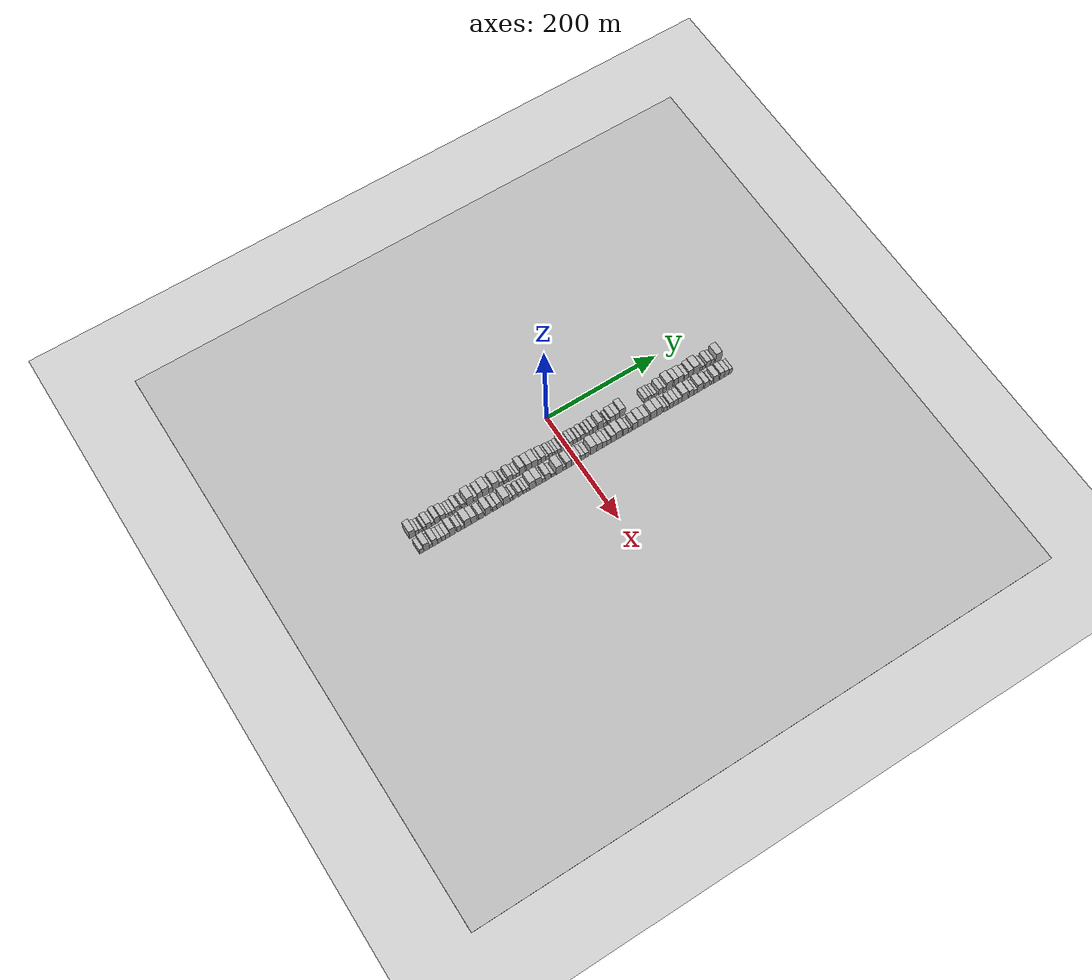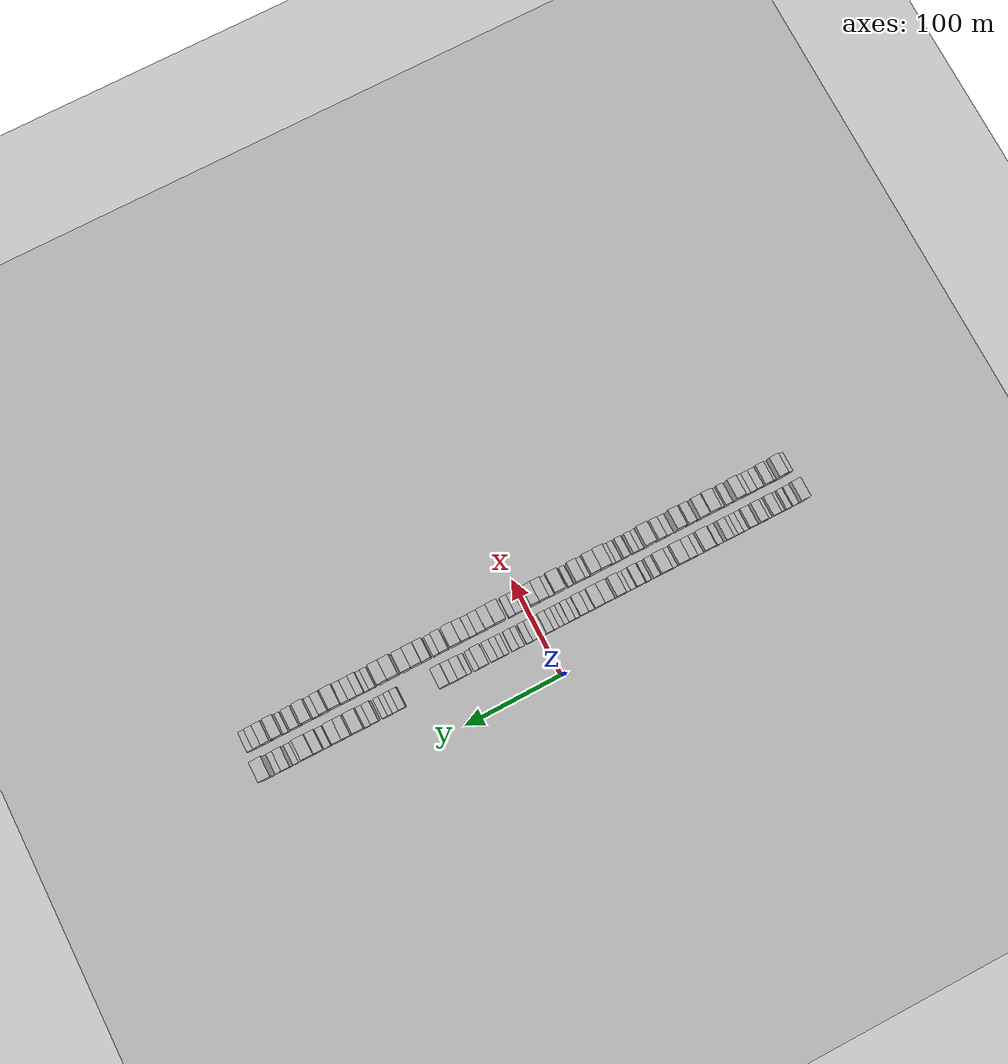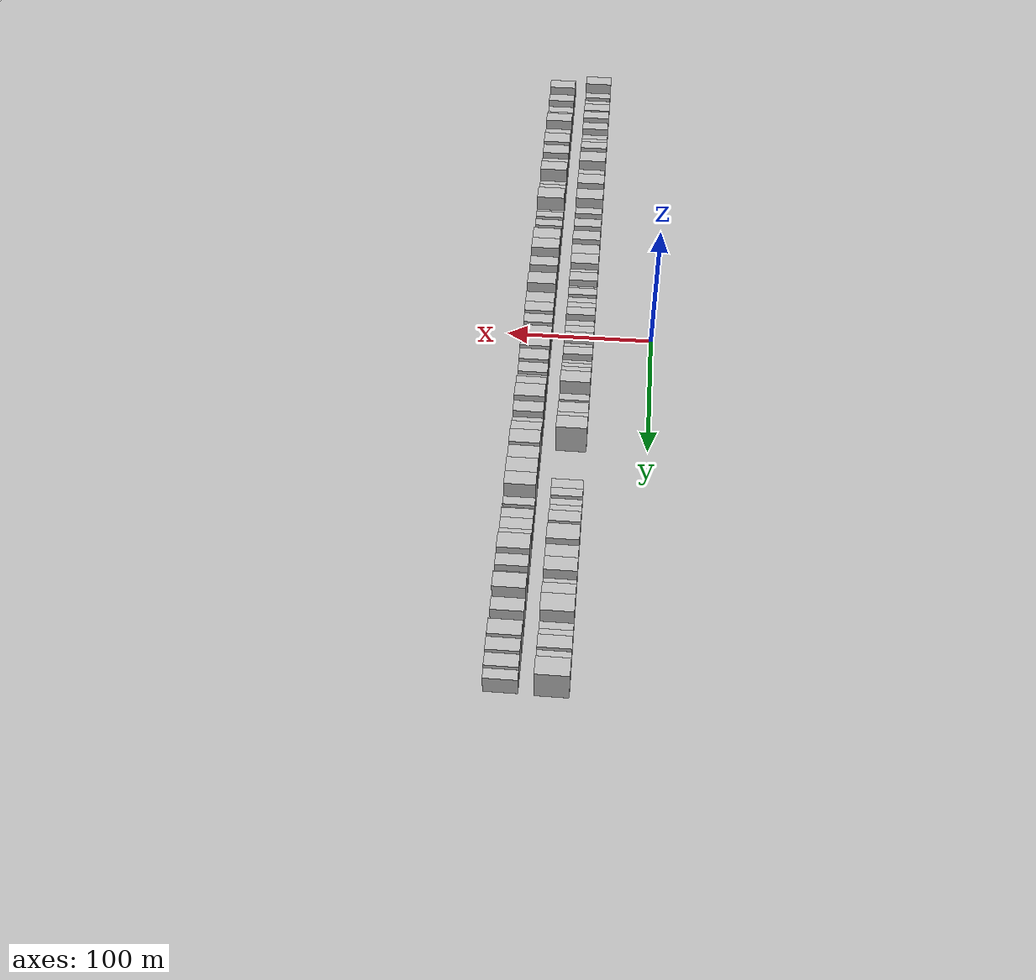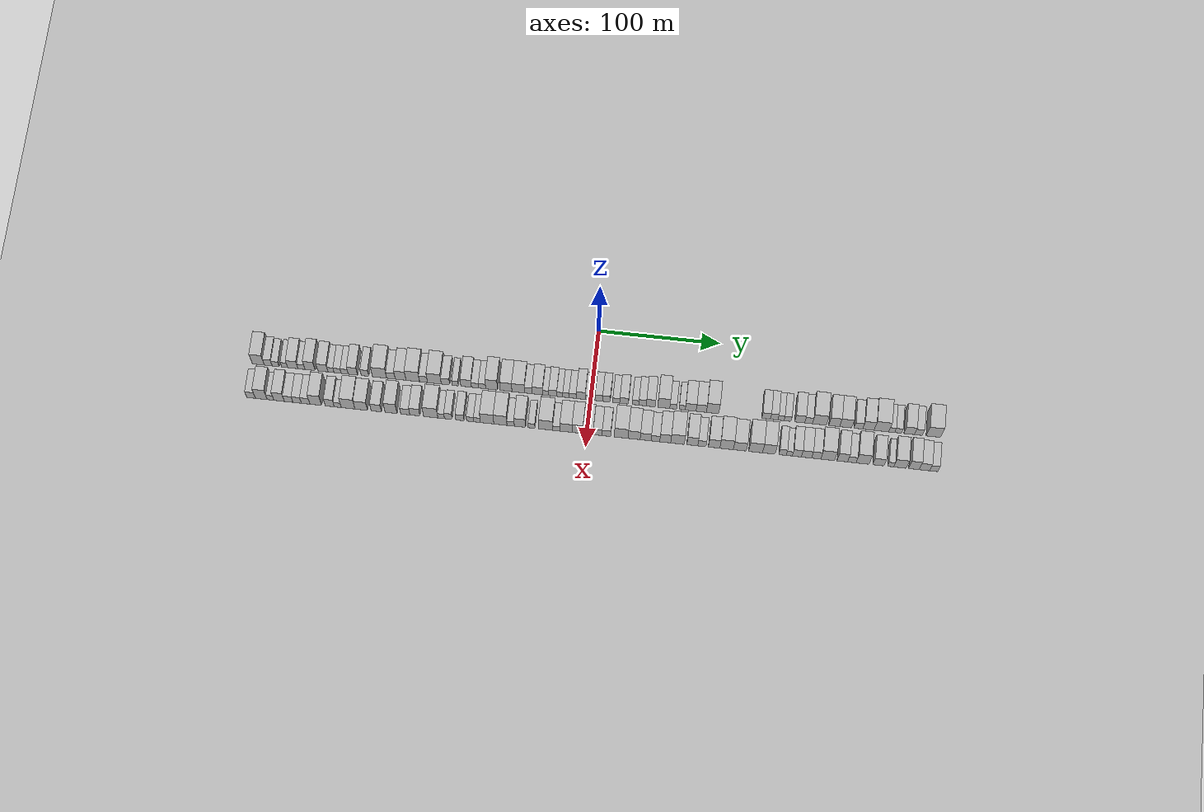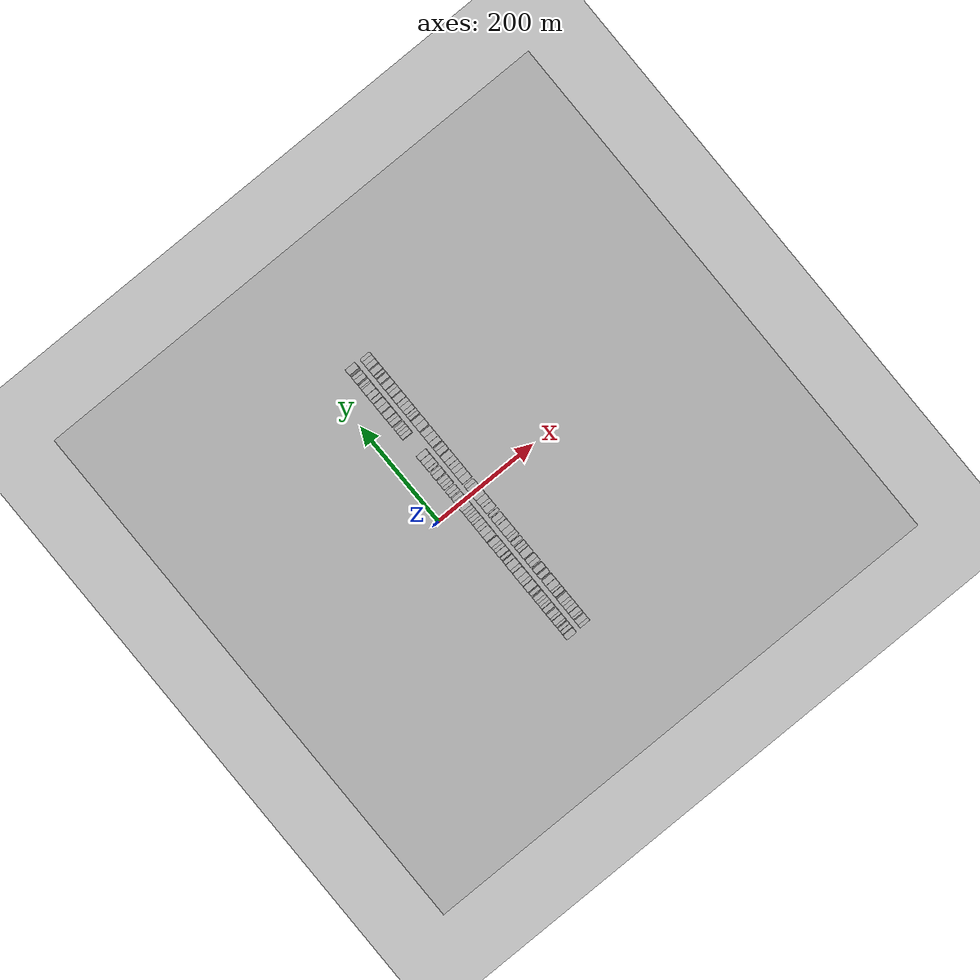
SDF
<?xml version="1.0" encoding="utf-8"?>

<sdf version="1.6">

   <world name="default">

      <gui fullscreen="0">

         <camera name="user_camera">

            <pose>-15 0 4.57585 0 0 0</pose>

            <view_controller>orbit</view_controller>

         </camera>

      </gui>

      <scene>

         <sky>

           <clouds>

             <speed>12</speed>

           </clouds>

         </sky>

         <ambient>0.4 0.4 0.4 1</ambient>

         <background>0.7 0.7 0.7 1</background>

         <shadows>1</shadows>

      </scene>

      <gravity>0 0 -9.8066</gravity>

      <magnetic_field>6e-06 2.3e-05 -4.2e-05</magnetic_field>

      <physics default="0" name="default_physics" type="ode">

         <ode>

            <solver>

               <type>quick</type>

               <iters>10</iters>

               <sor>1.0</sor>

               <use_dynamic_moi_rescaling>0</use_dynamic_moi_rescaling>

            </solver>

            <constraints>

               <cfm>0</cfm>

               <erp>0.2</erp>

               <contact_max_correcting_vel>100</contact_max_correcting_vel>

               <contact_surface_layer>0.001</contact_surface_layer>

            </constraints>

         </ode>

         <max_step_size>0.004</max_step_size>

         <real_time_factor>1</real_time_factor>

         <real_time_update_rate>250</real_time_update_rate>

      </physics>

      <light name="sun" type="directional">

         <cast_shadows>1</cast_shadows>

         <pose>0 0 10 0 0 0</pose>

         <diffuse>0.8 0.8 0.8 1</diffuse>

         <specular>0.2 0.2 0.2 1</specular>

         <attenuation>

            <range>1000</range>

            <constant>0.9</constant>

            <linear>0.01</linear>

            <quadratic>0.001</quadratic>

         </attenuation>

         <direction>-0.5 0.1 -0.9</direction>

      </light>

      <include>

         <name>ground_plane_1</name>

         <uri>model://HANNAS_ground_plane</uri>

         <pose>0 0 0  0 0 0</pose>

      </include>

      <include>

         <name>ground_plane_2</name>

         <uri>model://HANNAS_ground_plane</uri>

         <pose>100 0 0  0 0 0</pose>

      </include>

      <model name="building_1">

         <static>1</static>

         <pose frame="">50.0000 -273.0343 0 0.000000 0.000000 0.000000</pose>

         <link name="link">

            <pose frame="">0 0 12.00 0 0 0</pose>

            <collision name="collision">

               <geometry>

                  <box>

                     <size>20.0000 9.9314 24.0000</size>

                  </box>

               </geometry>

               <max_contacts>10</max_contacts>

               <surface>

                  <contact>

                     <ode/>

                  </contact>

                  <bounce/>

                  <friction>

                     <torsional>

                        <ode/>

                     </torsional>

                     <ode/>

                  </friction>

               </surface>

            </collision>

            <visual name="visual">

               <cast_shadows>0</cast_shadows>

               <geometry>

                  <box>

                     <size>20.0000 9.9314 24.0000</size>

                  </box>

               </geometry>

               <material>

                  <script>

                     <uri>model://HANNAS_wall/materials/scripts</uri>

                     <uri>model://HANNAS_wall/materials/textures</uri>

                     <name>vrc/HANNAS_wall</name>

                  </script>

               </material>

            </visual>

            <self_collide>0</self_collide>

            <enable_wind>0</enable_wind>

            <kinematic>0</kinematic>

         </link>

      </model>

      <model name="building_2">

         <static>1</static>

         <pose frame="">50.0000 -264.8588 0 0.000000 0.000000 0.000000</pose>

         <link name="link">

            <pose frame="">0 0 7.50 0 0 0</pose>

            <collision name="collision">

               <geometry>

                  <box>

                     <size>20.0000 6.4197 15.0000</size>

                  </box>

               </geometry>

               <max_contacts>10</max_contacts>

               <surface>

                  <contact>

                     <ode/>

                  </contact>

                  <bounce/>

                  <friction>

                     <torsional>

                        <ode/>

                     </torsional>

                     <ode/>

                  </friction>

               </surface>

            </collision>

            <visual name="visual">

               <cast_shadows>0</cast_shadows>

               <geometry>

                  <box>

                     <size>20.0000 6.4197 15.0000</size>

                  </box>

               </geometry>

               <material>

                  <script>

                     <uri>model://HANNAS_wall/materials/scripts</uri>

                     <uri>model://HANNAS_wall/materials/textures</uri>

                     <name>vrc/HANNAS_wall</name>

                  </script>

               </material>

            </visual>

            <self_collide>0</self_collide>

            <enable_wind>0</enable_wind>

            <kinematic>0</kinematic>

         </link>

      </model>

      <model name="building_3">

         <static>1</static>

         <pose frame="">50.0000 -258.8004 0 0.000000 0.000000 0.000000</pose>

         <link name="link">

            <pose frame="">0 0 6.00 0 0 0</pose>

            <collision name="collision">

               <geometry>

                  <box>

                     <size>20.0000 5.6971 12.0000</size>

                  </box>

               </geometry>

               <max_contacts>10</max_contacts>

               <surface>

                  <contact>

                     <ode/>

                  </contact>

                  <bounce/>

                  <friction>

                     <torsional>

                        <ode/>

                     </torsional>

                     <ode/>

                  </friction>

               </surface>

            </collision>

            <visual name="visual">

               <cast_shadows>0</cast_shadows>

               <geometry>

                  <box>

                     <size>20.0000 5.6971 12.0000</size>

                  </box>

               </geometry>

               <material>

                  <script>

                     <uri>model://HANNAS_wall/materials/scripts</uri>

                     <uri>model://HANNAS_wall/materials/textures</uri>

                     <name>vrc/HANNAS_wall</name>

                  </script>

               </material>

            </visual>

            <self_collide>0</self_collide>

            <enable_wind>0</enable_wind>

            <kinematic>0</kinematic>

         </link>

      </model>

      <model name="building_4">

         <static>1</static>

         <pose frame="">50.0000 -251.4891 0 0.000000 0.000000 0.000000</pose>

         <link name="link">

            <pose frame="">0 0 6.00 0 0 0</pose>

            <collision name="collision">

               <geometry>

                  <box>

                     <size>20.0000 4.9255 12.0000</size>

                  </box>

               </geometry>

               <max_contacts>10</max_contacts>

               <surface>

                  <contact>

                     <ode/>

                  </contact>

                  <bounce/>

                  <friction>

                     <torsional>

                        <ode/>

                     </torsional>

                     <ode/>

                  </friction>

               </surface>

            </collision>

            <visual name="visual">

               <cast_shadows>0</cast_shadows>

               <geometry>

                  <box>

                     <size>20.0000 4.9255 12.0000</size>

                  </box>

               </geometry>

               <material>

                  <script>

                     <uri>model://HANNAS_wall/materials/scripts</uri>

                     <uri>model://HANNAS_wall/materials/textures</uri>

                     <name>vrc/HANNAS_wall</name>

                  </script>

               </material>

            </visual>

            <self_collide>0</self_collide>

            <enable_wind>0</enable_wind>

            <kinematic>0</kinematic>

         </link>

      </model>

      <model name="building_5">

         <static>1</static>

         <pose frame="">50.0000 -244.7083 0 0.000000 0.000000 0.000000</pose>

         <link name="link">

            <pose frame="">0 0 9.00 0 0 0</pose>

            <collision name="collision">

               <geometry>

                  <box>

                     <size>20.0000 8.6361 18.0000</size>

                  </box>

               </geometry>

               <max_contacts>10</max_contacts>

               <surface>

                  <contact>

                     <ode/>

                  </contact>

                  <bounce/>

                  <friction>

                     <torsional>

                        <ode/>

                     </torsional>

                     <ode/>

                  </friction>

               </surface>

            </collision>

            <visual name="visual">

               <cast_shadows>0</cast_shadows>

               <geometry>

                  <box>

                     <size>20.0000 8.6361 18.0000</size>

                  </box>

               </geometry>

               <material>

                  <script>

                     <uri>model://HANNAS_wall/materials/scripts</uri>

                     <uri>model://HANNAS_wall/materials/textures</uri>

                     <name>vrc/HANNAS_wall</name>

                  </script>

               </material>

            </visual>

            <self_collide>0</self_collide>

            <enable_wind>0</enable_wind>

            <kinematic>0</kinematic>

         </link>

      </model>

      <model name="building_6">

         <static>1</static>

         <pose frame="">50.0000 -237.5211 0 0.000000 0.000000 0.000000</pose>

         <link name="link">

            <pose frame="">0 0 6.00 0 0 0</pose>

            <collision name="collision">

               <geometry>

                  <box>

                     <size>20.0000 5.7383 12.0000</size>

                  </box>

               </geometry>

               <max_contacts>10</max_contacts>

               <surface>

                  <contact>

                     <ode/>

                  </contact>

                  <bounce/>

                  <friction>

                     <torsional>

                        <ode/>

                     </torsional>

                     <ode/>

                  </friction>

               </surface>

            </collision>

            <visual name="visual">

               <cast_shadows>0</cast_shadows>

               <geometry>

                  <box>

                     <size>20.0000 5.7383 12.0000</size>

                  </box>

               </geometry>

               <material>

                  <script>

                     <uri>model://HANNAS_wall/materials/scripts</uri>

                     <uri>model://HANNAS_wall/materials/textures</uri>

                     <name>vrc/HANNAS_wall</name>

                  </script>

               </material>

            </visual>

            <self_collide>0</self_collide>

            <enable_wind>0</enable_wind>

            <kinematic>0</kinematic>

         </link>

      </model>

      <model name="building_7">

         <static>1</static>

         <pose frame="">50.0000 -230.3885 0 0.000000 0.000000 0.000000</pose>

         <link name="link">

            <pose frame="">0 0 10.50 0 0 0</pose>

            <collision name="collision">

               <geometry>

                  <box>

                     <size>20.0000 8.5270 21.0000</size>

                  </box>

               </geometry>

               <max_contacts>10</max_contacts>

               <surface>

                  <contact>

                     <ode/>

                  </contact>

                  <bounce/>

                  <friction>

                     <torsional>

                        <ode/>

                     </torsional>

                     <ode/>

                  </friction>

               </surface>

            </collision>

            <visual name="visual">

               <cast_shadows>0</cast_shadows>

               <geometry>

                  <box>

                     <size>20.0000 8.5270 21.0000</size>

                  </box>

               </geometry>

               <material>

                  <script>

                     <uri>model://HANNAS_wall/materials/scripts</uri>

                     <uri>model://HANNAS_wall/materials/textures</uri>

                     <name>vrc/HANNAS_wall</name>

                  </script>

               </material>

            </visual>

            <self_collide>0</self_collide>

            <enable_wind>0</enable_wind>

            <kinematic>0</kinematic>

         </link>

      </model>

      <model name="building_8">

         <static>1</static>

         <pose frame="">50.0000 -219.9198 0 0.000000 0.000000 0.000000</pose>

         <link name="link">

            <pose frame="">0 0 9.00 0 0 0</pose>

            <collision name="collision">

               <geometry>

                  <box>

                     <size>20.0000 8.4104 18.0000</size>

                  </box>

               </geometry>

               <max_contacts>10</max_contacts>

               <surface>

                  <contact>

                     <ode/>

                  </contact>

                  <bounce/>

                  <friction>

                     <torsional>

                        <ode/>

                     </torsional>

                     <ode/>

                  </friction>

               </surface>

            </collision>

            <visual name="visual">

               <cast_shadows>0</cast_shadows>

               <geometry>

                  <box>

                     <size>20.0000 8.4104 18.0000</size>

                  </box>

               </geometry>

               <material>

                  <script>

                     <uri>model://HANNAS_wall/materials/scripts</uri>

                     <uri>model://HANNAS_wall/materials/textures</uri>

                     <name>vrc/HANNAS_wall</name>

                  </script>

               </material>

            </visual>

            <self_collide>0</self_collide>

            <enable_wind>0</enable_wind>

            <kinematic>0</kinematic>

         </link>

      </model>

      <model name="building_9">

         <static>1</static>

         <pose frame="">50.0000 -213.1879 0 0.000000 0.000000 0.000000</pose>

         <link name="link">

            <pose frame="">0 0 6.00 0 0 0</pose>

            <collision name="collision">

               <geometry>

                  <box>

                     <size>20.0000 5.0536 12.0000</size>

                  </box>

               </geometry>

               <max_contacts>10</max_contacts>

               <surface>

                  <contact>

                     <ode/>

                  </contact>

                  <bounce/>

                  <friction>

                     <torsional>

                        <ode/>

                     </torsional>

                     <ode/>

                  </friction>

               </surface>

            </collision>

            <visual name="visual">

               <cast_shadows>0</cast_shadows>

               <geometry>

                  <box>

                     <size>20.0000 5.0536 12.0000</size>

                  </box>

               </geometry>

               <material>

                  <script>

                     <uri>model://HANNAS_wall/materials/scripts</uri>

                     <uri>model://HANNAS_wall/materials/textures</uri>

                     <name>vrc/HANNAS_wall</name>

                  </script>

               </material>

            </visual>

            <self_collide>0</self_collide>

            <enable_wind>0</enable_wind>

            <kinematic>0</kinematic>

         </link>

      </model>

      <model name="building_10">

         <static>1</static>

         <pose frame="">50.0000 -207.7523 0 0.000000 0.000000 0.000000</pose>

         <link name="link">

            <pose frame="">0 0 6.00 0 0 0</pose>

            <collision name="collision">

               <geometry>

                  <box>

                     <size>20.0000 5.8176 12.0000</size>

                  </box>

               </geometry>

               <max_contacts>10</max_contacts>

               <surface>

                  <contact>

                     <ode/>

                  </contact>

                  <bounce/>

                  <friction>

                     <torsional>

                        <ode/>

                     </torsional>

                     <ode/>

                  </friction>

               </surface>

            </collision>

            <visual name="visual">

               <cast_shadows>0</cast_shadows>

               <geometry>

                  <box>

                     <size>20.0000 5.8176 12.0000</size>

                  </box>

               </geometry>

               <material>

                  <script>

                     <uri>model://HANNAS_wall/materials/scripts</uri>

                     <uri>model://HANNAS_wall/materials/textures</uri>

                     <name>vrc/HANNAS_wall</name>

                  </script>

               </material>

            </visual>

            <self_collide>0</self_collide>

            <enable_wind>0</enable_wind>

            <kinematic>0</kinematic>

         </link>

      </model>

      <model name="building_11">

         <static>1</static>

         <pose frame="">50.0000 -201.9945 0 0.000000 0.000000 0.000000</pose>

         <link name="link">

            <pose frame="">0 0 6.00 0 0 0</pose>

            <collision name="collision">

               <geometry>

                  <box>

                     <size>20.0000 5.6979 12.0000</size>

                  </box>

               </geometry>

               <max_contacts>10</max_contacts>

               <surface>

                  <contact>

                     <ode/>

                  </contact>

                  <bounce/>

                  <friction>

                     <torsional>

                        <ode/>

                     </torsional>

                     <ode/>

                  </friction>

               </surface>

            </collision>

            <visual name="visual">

               <cast_shadows>0</cast_shadows>

               <geometry>

                  <box>

                     <size>20.0000 5.6979 12.0000</size>

                  </box>

               </geometry>

               <material>

                  <script>

                     <uri>model://HANNAS_wall/materials/scripts</uri>

                     <uri>model://HANNAS_wall/materials/textures</uri>

                     <name>vrc/HANNAS_wall</name>

                  </script>

               </material>

            </visual>

            <self_collide>0</self_collide>

            <enable_wind>0</enable_wind>

            <kinematic>0</kinematic>

         </link>

      </model>

      <model name="building_12">

         <static>1</static>

         <pose frame="">50.0000 -195.2230 0 0.000000 0.000000 0.000000</pose>

         <link name="link">

            <pose frame="">0 0 9.00 0 0 0</pose>

            <collision name="collision">

               <geometry>

                  <box>

                     <size>20.0000 7.8452 18.0000</size>

                  </box>

               </geometry>

               <max_contacts>10</max_contacts>

               <surface>

                  <contact>

                     <ode/>

                  </contact>

                  <bounce/>

                  <friction>

                     <torsional>

                        <ode/>

                     </torsional>

                     <ode/>

                  </friction>

               </surface>

            </collision>

            <visual name="visual">

               <cast_shadows>0</cast_shadows>

               <geometry>

                  <box>

                     <size>20.0000 7.8452 18.0000</size>

                  </box>

               </geometry>

               <material>

                  <script>

                     <uri>model://HANNAS_wall/materials/scripts</uri>

                     <uri>model://HANNAS_wall/materials/textures</uri>

                     <name>vrc/HANNAS_wall</name>

                  </script>

               </material>

            </visual>

            <self_collide>0</self_collide>

            <enable_wind>0</enable_wind>

            <kinematic>0</kinematic>

         </link>

      </model>

      <model name="building_13">

         <static>1</static>

         <pose frame="">50.0000 -185.1870 0 0.000000 0.000000 0.000000</pose>

         <link name="link">

            <pose frame="">0 0 7.50 0 0 0</pose>

            <collision name="collision">

               <geometry>

                  <box>

                     <size>20.0000 6.2269 15.0000</size>

                  </box>

               </geometry>

               <max_contacts>10</max_contacts>

               <surface>

                  <contact>

                     <ode/>

                  </contact>

                  <bounce/>

                  <friction>

                     <torsional>

                        <ode/>

                     </torsional>

                     <ode/>

                  </friction>

               </surface>

            </collision>

            <visual name="visual">

               <cast_shadows>0</cast_shadows>

               <geometry>

                  <box>

                     <size>20.0000 6.2269 15.0000</size>

                  </box>

               </geometry>

               <material>

                  <script>

                     <uri>model://HANNAS_wall/materials/scripts</uri>

                     <uri>model://HANNAS_wall/materials/textures</uri>

                     <name>vrc/HANNAS_wall</name>

                  </script>

               </material>

            </visual>

            <self_collide>0</self_collide>

            <enable_wind>0</enable_wind>

            <kinematic>0</kinematic>

         </link>

      </model>

      <model name="building_14">

         <static>1</static>

         <pose frame="">50.0000 -173.2134 0 0.000000 0.000000 0.000000</pose>

         <link name="link">

            <pose frame="">0 0 12.00 0 0 0</pose>

            <collision name="collision">

               <geometry>

                  <box>

                     <size>20.0000 11.7202 24.0000</size>

                  </box>

               </geometry>

               <max_contacts>10</max_contacts>

               <surface>

                  <contact>

                     <ode/>

                  </contact>

                  <bounce/>

                  <friction>

                     <torsional>

                        <ode/>

                     </torsional>

                     <ode/>

                  </friction>

               </surface>

            </collision>

            <visual name="visual">

               <cast_shadows>0</cast_shadows>

               <geometry>

                  <box>

                     <size>20.0000 11.7202 24.0000</size>

                  </box>

               </geometry>

               <material>

                  <script>

                     <uri>model://HANNAS_wall/materials/scripts</uri>

                     <uri>model://HANNAS_wall/materials/textures</uri>

                     <name>vrc/HANNAS_wall</name>

                  </script>

               </material>

            </visual>

            <self_collide>0</self_collide>

            <enable_wind>0</enable_wind>

            <kinematic>0</kinematic>

         </link>

      </model>

      <model name="building_15">

         <static>1</static>

         <pose frame="">50.0000 -163.8591 0 0.000000 0.000000 0.000000</pose>

         <link name="link">

            <pose frame="">0 0 7.50 0 0 0</pose>

            <collision name="collision">

               <geometry>

                  <box>

                     <size>20.0000 6.9883 15.0000</size>

                  </box>

               </geometry>

               <max_contacts>10</max_contacts>

               <surface>

                  <contact>

                     <ode/>

                  </contact>

                  <bounce/>

                  <friction>

                     <torsional>

                        <ode/>

                     </torsional>

                     <ode/>

                  </friction>

               </surface>

            </collision>

            <visual name="visual">

               <cast_shadows>0</cast_shadows>

               <geometry>

                  <box>

                     <size>20.0000 6.9883 15.0000</size>

                  </box>

               </geometry>

               <material>

                  <script>

                     <uri>model://HANNAS_wall/materials/scripts</uri>

                     <uri>model://HANNAS_wall/materials/textures</uri>

                     <name>vrc/HANNAS_wall</name>

                  </script>

               </material>

            </visual>

            <self_collide>0</self_collide>

            <enable_wind>0</enable_wind>

            <kinematic>0</kinematic>

         </link>

      </model>

      <model name="building_16">

         <static>1</static>

         <pose frame="">50.0000 -155.9668 0 0.000000 0.000000 0.000000</pose>

         <link name="link">

            <pose frame="">0 0 10.50 0 0 0</pose>

            <collision name="collision">

               <geometry>

                  <box>

                     <size>20.0000 8.7963 21.0000</size>

                  </box>

               </geometry>

               <max_contacts>10</max_contacts>

               <surface>

                  <contact>

                     <ode/>

                  </contact>

                  <bounce/>

                  <friction>

                     <torsional>

                        <ode/>

                     </torsional>

                     <ode/>

                  </friction>

               </surface>

            </collision>

            <visual name="visual">

               <cast_shadows>0</cast_shadows>

               <geometry>

                  <box>

                     <size>20.0000 8.7963 21.0000</size>

                  </box>

               </geometry>

               <material>

                  <script>

                     <uri>model://HANNAS_wall/materials/scripts</uri>

                     <uri>model://HANNAS_wall/materials/textures</uri>

                     <name>vrc/HANNAS_wall</name>

                  </script>

               </material>

            </visual>

            <self_collide>0</self_collide>

            <enable_wind>0</enable_wind>

            <kinematic>0</kinematic>

         </link>

      </model>

      <model name="building_17">

         <static>1</static>

         <pose frame="">50.0000 -145.9873 0 0.000000 0.000000 0.000000</pose>

         <link name="link">

            <pose frame="">0 0 12.00 0 0 0</pose>

            <collision name="collision">

               <geometry>

                  <box>

                     <size>20.0000 11.1627 24.0000</size>

                  </box>

               </geometry>

               <max_contacts>10</max_contacts>

               <surface>

                  <contact>

                     <ode/>

                  </contact>

                  <bounce/>

                  <friction>

                     <torsional>

                        <ode/>

                     </torsional>

                     <ode/>

                  </friction>

               </surface>

            </collision>

            <visual name="visual">

               <cast_shadows>0</cast_shadows>

               <geometry>

                  <box>

                     <size>20.0000 11.1627 24.0000</size>

                  </box>

               </geometry>

               <material>

                  <script>

                     <uri>model://HANNAS_wall/materials/scripts</uri>

                     <uri>model://HANNAS_wall/materials/textures</uri>

                     <name>vrc/HANNAS_wall</name>

                  </script>

               </material>

            </visual>

            <self_collide>0</self_collide>

            <enable_wind>0</enable_wind>

            <kinematic>0</kinematic>

         </link>

      </model>

      <model name="building_18">

         <static>1</static>

         <pose frame="">50.0000 -137.1092 0 0.000000 0.000000 0.000000</pose>

         <link name="link">

            <pose frame="">0 0 7.50 0 0 0</pose>

            <collision name="collision">

               <geometry>

                  <box>

                     <size>20.0000 6.5936 15.0000</size>

                  </box>

               </geometry>

               <max_contacts>10</max_contacts>

               <surface>

                  <contact>

                     <ode/>

                  </contact>

                  <bounce/>

                  <friction>

                     <torsional>

                        <ode/>

                     </torsional>

                     <ode/>

                  </friction>

               </surface>

            </collision>

            <visual name="visual">

               <cast_shadows>0</cast_shadows>

               <geometry>

                  <box>

                     <size>20.0000 6.5936 15.0000</size>

                  </box>

               </geometry>

               <material>

                  <script>

                     <uri>model://HANNAS_wall/materials/scripts</uri>

                     <uri>model://HANNAS_wall/materials/textures</uri>

                     <name>vrc/HANNAS_wall</name>

                  </script>

               </material>

            </visual>

            <self_collide>0</self_collide>

            <enable_wind>0</enable_wind>

            <kinematic>0</kinematic>

         </link>

      </model>

      <model name="building_19">

         <static>1</static>

         <pose frame="">50.0000 -128.1583 0 0.000000 0.000000 0.000000</pose>

         <link name="link">

            <pose frame="">0 0 12.00 0 0 0</pose>

            <collision name="collision">

               <geometry>

                  <box>

                     <size>20.0000 11.3082 24.0000</size>

                  </box>

               </geometry>

               <max_contacts>10</max_contacts>

               <surface>

                  <contact>

                     <ode/>

                  </contact>

                  <bounce/>

                  <friction>

                     <torsional>

                        <ode/>

                     </torsional>

                     <ode/>

                  </friction>

               </surface>

            </collision>

            <visual name="visual">

               <cast_shadows>0</cast_shadows>

               <geometry>

                  <box>

                     <size>20.0000 11.3082 24.0000</size>

                  </box>

               </geometry>

               <material>

                  <script>

                     <uri>model://HANNAS_wall/materials/scripts</uri>

                     <uri>model://HANNAS_wall/materials/textures</uri>

                     <name>vrc/HANNAS_wall</name>

                  </script>

               </material>

            </visual>

            <self_collide>0</self_collide>

            <enable_wind>0</enable_wind>

            <kinematic>0</kinematic>

         </link>

      </model>

      <model name="building_20">

         <static>1</static>

         <pose frame="">50.0000 -119.0666 0 0.000000 0.000000 0.000000</pose>

         <link name="link">

            <pose frame="">0 0 7.50 0 0 0</pose>

            <collision name="collision">

               <geometry>

                  <box>

                     <size>20.0000 6.8751 15.0000</size>

                  </box>

               </geometry>

               <max_contacts>10</max_contacts>

               <surface>

                  <contact>

                     <ode/>

                  </contact>

                  <bounce/>

                  <friction>

                     <torsional>

                        <ode/>

                     </torsional>

                     <ode/>

                  </friction>

               </surface>

            </collision>

            <visual name="visual">

               <cast_shadows>0</cast_shadows>

               <geometry>

                  <box>

                     <size>20.0000 6.8751 15.0000</size>

                  </box>

               </geometry>

               <material>

                  <script>

                     <uri>model://HANNAS_wall/materials/scripts</uri>

                     <uri>model://HANNAS_wall/materials/textures</uri>

                     <name>vrc/HANNAS_wall</name>

                  </script>

               </material>

            </visual>

            <self_collide>0</self_collide>

            <enable_wind>0</enable_wind>

            <kinematic>0</kinematic>

         </link>

      </model>

      <model name="building_21">

         <static>1</static>

         <pose frame="">50.0000 -111.0815 0 0.000000 0.000000 0.000000</pose>

         <link name="link">

            <pose frame="">0 0 6.00 0 0 0</pose>

            <collision name="collision">

               <geometry>

                  <box>

                     <size>20.0000 5.0952 12.0000</size>

                  </box>

               </geometry>

               <max_contacts>10</max_contacts>

               <surface>

                  <contact>

                     <ode/>

                  </contact>

                  <bounce/>

                  <friction>

                     <torsional>

                        <ode/>

                     </torsional>

                     <ode/>

                  </friction>

               </surface>

            </collision>

            <visual name="visual">

               <cast_shadows>0</cast_shadows>

               <geometry>

                  <box>

                     <size>20.0000 5.0952 12.0000</size>

                  </box>

               </geometry>

               <material>

                  <script>

                     <uri>model://HANNAS_wall/materials/scripts</uri>

                     <uri>model://HANNAS_wall/materials/textures</uri>

                     <name>vrc/HANNAS_wall</name>

                  </script>

               </material>

            </visual>

            <self_collide>0</self_collide>

            <enable_wind>0</enable_wind>

            <kinematic>0</kinematic>

         </link>

      </model>

      <model name="building_22">

         <static>1</static>

         <pose frame="">50.0000 -102.1809 0 0.000000 0.000000 0.000000</pose>

         <link name="link">

            <pose frame="">0 0 9.00 0 0 0</pose>

            <collision name="collision">

               <geometry>

                  <box>

                     <size>20.0000 8.7060 18.0000</size>

                  </box>

               </geometry>

               <max_contacts>10</max_contacts>

               <surface>

                  <contact>

                     <ode/>

                  </contact>

                  <bounce/>

                  <friction>

                     <torsional>

                        <ode/>

                     </torsional>

                     <ode/>

                  </friction>

               </surface>

            </collision>

            <visual name="visual">

               <cast_shadows>0</cast_shadows>

               <geometry>

                  <box>

                     <size>20.0000 8.7060 18.0000</size>

                  </box>

               </geometry>

               <material>

                  <script>

                     <uri>model://HANNAS_wall/materials/scripts</uri>

                     <uri>model://HANNAS_wall/materials/textures</uri>

                     <name>vrc/HANNAS_wall</name>

                  </script>

               </material>

            </visual>

            <self_collide>0</self_collide>

            <enable_wind>0</enable_wind>

            <kinematic>0</kinematic>

         </link>

      </model>

      <model name="building_23">

         <static>1</static>

         <pose frame="">50.0000 -94.8790 0 0.000000 0.000000 0.000000</pose>

         <link name="link">

            <pose frame="">0 0 6.00 0 0 0</pose>

            <collision name="collision">

               <geometry>

                  <box>

                     <size>20.0000 5.8978 12.0000</size>

                  </box>

               </geometry>

               <max_contacts>10</max_contacts>

               <surface>

                  <contact>

                     <ode/>

                  </contact>

                  <bounce/>

                  <friction>

                     <torsional>

                        <ode/>

                     </torsional>

                     <ode/>

                  </friction>

               </surface>

            </collision>

            <visual name="visual">

               <cast_shadows>0</cast_shadows>

               <geometry>

                  <box>

                     <size>20.0000 5.8978 12.0000</size>

                  </box>

               </geometry>

               <material>

                  <script>

                     <uri>model://HANNAS_wall/materials/scripts</uri>

                     <uri>model://HANNAS_wall/materials/textures</uri>

                     <name>vrc/HANNAS_wall</name>

                  </script>

               </material>

            </visual>

            <self_collide>0</self_collide>

            <enable_wind>0</enable_wind>

            <kinematic>0</kinematic>

         </link>

      </model>

      <model name="building_24">

         <static>1</static>

         <pose frame="">50.0000 -89.0236 0 0.000000 0.000000 0.000000</pose>

         <link name="link">

            <pose frame="">0 0 6.00 0 0 0</pose>

            <collision name="collision">

               <geometry>

                  <box>

                     <size>20.0000 5.8129 12.0000</size>

                  </box>

               </geometry>

               <max_contacts>10</max_contacts>

               <surface>

                  <contact>

                     <ode/>

                  </contact>

                  <bounce/>

                  <friction>

                     <torsional>

                        <ode/>

                     </torsional>

                     <ode/>

                  </friction>

               </surface>

            </collision>

            <visual name="visual">

               <cast_shadows>0</cast_shadows>

               <geometry>

                  <box>

                     <size>20.0000 5.8129 12.0000</size>

                  </box>

               </geometry>

               <material>

                  <script>

                     <uri>model://HANNAS_wall/materials/scripts</uri>

                     <uri>model://HANNAS_wall/materials/textures</uri>

                     <name>vrc/HANNAS_wall</name>

                  </script>

               </material>

            </visual>

            <self_collide>0</self_collide>

            <enable_wind>0</enable_wind>

            <kinematic>0</kinematic>

         </link>

      </model>

      <model name="building_25">

         <static>1</static>

         <pose frame="">50.0000 -81.2553 0 0.000000 0.000000 0.000000</pose>

         <link name="link">

            <pose frame="">0 0 12.00 0 0 0</pose>

            <collision name="collision">

               <geometry>

                  <box>

                     <size>20.0000 9.7238 24.0000</size>

                  </box>

               </geometry>

               <max_contacts>10</max_contacts>

               <surface>

                  <contact>

                     <ode/>

                  </contact>

                  <bounce/>

                  <friction>

                     <torsional>

                        <ode/>

                     </torsional>

                     <ode/>

                  </friction>

               </surface>

            </collision>

            <visual name="visual">

               <cast_shadows>0</cast_shadows>

               <geometry>

                  <box>

                     <size>20.0000 9.7238 24.0000</size>

                  </box>

               </geometry>

               <material>

                  <script>

                     <uri>model://HANNAS_wall/materials/scripts</uri>

                     <uri>model://HANNAS_wall/materials/textures</uri>

                     <name>vrc/HANNAS_wall</name>

                  </script>

               </material>

            </visual>

            <self_collide>0</self_collide>

            <enable_wind>0</enable_wind>

            <kinematic>0</kinematic>

         </link>

      </model>

      <model name="building_26">

         <static>1</static>

         <pose frame="">50.0000 -69.5122 0 0.000000 0.000000 0.000000</pose>

         <link name="link">

            <pose frame="">0 0 10.50 0 0 0</pose>

            <collision name="collision">

               <geometry>

                  <box>

                     <size>20.0000 9.7625 21.0000</size>

                  </box>

               </geometry>

               <max_contacts>10</max_contacts>

               <surface>

                  <contact>

                     <ode/>

                  </contact>

                  <bounce/>

                  <friction>

                     <torsional>

                        <ode/>

                     </torsional>

                     <ode/>

                  </friction>

               </surface>

            </collision>

            <visual name="visual">

               <cast_shadows>0</cast_shadows>

               <geometry>

                  <box>

                     <size>20.0000 9.7625 21.0000</size>

                  </box>

               </geometry>

               <material>

                  <script>

                     <uri>model://HANNAS_wall/materials/scripts</uri>

                     <uri>model://HANNAS_wall/materials/textures</uri>

                     <name>vrc/HANNAS_wall</name>

                  </script>

               </material>

            </visual>

            <self_collide>0</self_collide>

            <enable_wind>0</enable_wind>

            <kinematic>0</kinematic>

         </link>

      </model>

      <model name="building_27">

         <static>1</static>

         <pose frame="">50.0000 -59.4392 0 0.000000 0.000000 0.000000</pose>

         <link name="link">

            <pose frame="">0 0 10.50 0 0 0</pose>

            <collision name="collision">

               <geometry>

                  <box>

                     <size>20.0000 10.3836 21.0000</size>

                  </box>

               </geometry>

               <max_contacts>10</max_contacts>

               <surface>

                  <contact>

                     <ode/>

                  </contact>

                  <bounce/>

                  <friction>

                     <torsional>

                        <ode/>

                     </torsional>

                     <ode/>

                  </friction>

               </surface>

            </collision>

            <visual name="visual">

               <cast_shadows>0</cast_shadows>

               <geometry>

                  <box>

                     <size>20.0000 10.3836 21.0000</size>

                  </box>

               </geometry>

               <material>

                  <script>

                     <uri>model://HANNAS_wall/materials/scripts</uri>

                     <uri>model://HANNAS_wall/materials/textures</uri>

                     <name>vrc/HANNAS_wall</name>

                  </script>

               </material>

            </visual>

            <self_collide>0</self_collide>

            <enable_wind>0</enable_wind>

            <kinematic>0</kinematic>

         </link>

      </model>

      <model name="building_28">

         <static>1</static>

         <pose frame="">50.0000 -51.1860 0 0.000000 0.000000 0.000000</pose>

         <link name="link">

            <pose frame="">0 0 7.50 0 0 0</pose>

            <collision name="collision">

               <geometry>

                  <box>

                     <size>20.0000 6.1228 15.0000</size>

                  </box>

               </geometry>

               <max_contacts>10</max_contacts>

               <surface>

                  <contact>

                     <ode/>

                  </contact>

                  <bounce/>

                  <friction>

                     <torsional>

                        <ode/>

                     </torsional>

                     <ode/>

                  </friction>

               </surface>

            </collision>

            <visual name="visual">

               <cast_shadows>0</cast_shadows>

               <geometry>

                  <box>

                     <size>20.0000 6.1228 15.0000</size>

                  </box>

               </geometry>

               <material>

                  <script>

                     <uri>model://HANNAS_wall/materials/scripts</uri>

                     <uri>model://HANNAS_wall/materials/textures</uri>

                     <name>vrc/HANNAS_wall</name>

                  </script>

               </material>

            </visual>

            <self_collide>0</self_collide>

            <enable_wind>0</enable_wind>

            <kinematic>0</kinematic>

         </link>

      </model>

      <model name="building_29">

         <static>1</static>

         <pose frame="">50.0000 -43.8000 0 0.000000 0.000000 0.000000</pose>

         <link name="link">

            <pose frame="">0 0 9.00 0 0 0</pose>

            <collision name="collision">

               <geometry>

                  <box>

                     <size>20.0000 8.6491 18.0000</size>

                  </box>

               </geometry>

               <max_contacts>10</max_contacts>

               <surface>

                  <contact>

                     <ode/>

                  </contact>

                  <bounce/>

                  <friction>

                     <torsional>

                        <ode/>

                     </torsional>

                     <ode/>

                  </friction>

               </surface>

            </collision>

            <visual name="visual">

               <cast_shadows>0</cast_shadows>

               <geometry>

                  <box>

                     <size>20.0000 8.6491 18.0000</size>

                  </box>

               </geometry>

               <material>

                  <script>

                     <uri>model://HANNAS_wall/materials/scripts</uri>

                     <uri>model://HANNAS_wall/materials/textures</uri>

                     <name>vrc/HANNAS_wall</name>

                  </script>

               </material>

            </visual>

            <self_collide>0</self_collide>

            <enable_wind>0</enable_wind>

            <kinematic>0</kinematic>

         </link>

      </model>

      <model name="building_30">

         <static>1</static>

         <pose frame="">50.0000 -37.0525 0 0.000000 0.000000 0.000000</pose>

         <link name="link">

            <pose frame="">0 0 6.00 0 0 0</pose>

            <collision name="collision">

               <geometry>

                  <box>

                     <size>20.0000 4.8459 12.0000</size>

                  </box>

               </geometry>

               <max_contacts>10</max_contacts>

               <surface>

                  <contact>

                     <ode/>

                  </contact>

                  <bounce/>

                  <friction>

                     <torsional>

                        <ode/>

                     </torsional>

                     <ode/>

                  </friction>

               </surface>

            </collision>

            <visual name="visual">

               <cast_shadows>0</cast_shadows>

               <geometry>

                  <box>

                     <size>20.0000 4.8459 12.0000</size>

                  </box>

               </geometry>

               <material>

                  <script>

                     <uri>model://HANNAS_wall/materials/scripts</uri>

                     <uri>model://HANNAS_wall/materials/textures</uri>

                     <name>vrc/HANNAS_wall</name>

                  </script>

               </material>

            </visual>

            <self_collide>0</self_collide>

            <enable_wind>0</enable_wind>

            <kinematic>0</kinematic>

         </link>

      </model>

      <model name="building_31">

         <static>1</static>

         <pose frame="">50.0000 -31.2973 0 0.000000 0.000000 0.000000</pose>

         <link name="link">

            <pose frame="">0 0 7.50 0 0 0</pose>

            <collision name="collision">

               <geometry>

                  <box>

                     <size>20.0000 6.6644 15.0000</size>

                  </box>

               </geometry>

               <max_contacts>10</max_contacts>

               <surface>

                  <contact>

                     <ode/>

                  </contact>

                  <bounce/>

                  <friction>

                     <torsional>

                        <ode/>

                     </torsional>

                     <ode/>

                  </friction>

               </surface>

            </collision>

            <visual name="visual">

               <cast_shadows>0</cast_shadows>

               <geometry>

                  <box>

                     <size>20.0000 6.6644 15.0000</size>

                  </box>

               </geometry>

               <material>

                  <script>

                     <uri>model://HANNAS_wall/materials/scripts</uri>

                     <uri>model://HANNAS_wall/materials/textures</uri>

                     <name>vrc/HANNAS_wall</name>

                  </script>

               </material>

            </visual>

            <self_collide>0</self_collide>

            <enable_wind>0</enable_wind>

            <kinematic>0</kinematic>

         </link>

      </model>

      <model name="building_32">

         <static>1</static>

         <pose frame="">50.0000 -25.5076 0 0.000000 0.000000 0.000000</pose>

         <link name="link">

            <pose frame="">0 0 6.00 0 0 0</pose>

            <collision name="collision">

               <geometry>

                  <box>

                     <size>20.0000 4.9150 12.0000</size>

                  </box>

               </geometry>

               <max_contacts>10</max_contacts>

               <surface>

                  <contact>

                     <ode/>

                  </contact>

                  <bounce/>

                  <friction>

                     <torsional>

                        <ode/>

                     </torsional>

                     <ode/>

                  </friction>

               </surface>

            </collision>

            <visual name="visual">

               <cast_shadows>0</cast_shadows>

               <geometry>

                  <box>

                     <size>20.0000 4.9150 12.0000</size>

                  </box>

               </geometry>

               <material>

                  <script>

                     <uri>model://HANNAS_wall/materials/scripts</uri>

                     <uri>model://HANNAS_wall/materials/textures</uri>

                     <name>vrc/HANNAS_wall</name>

                  </script>

               </material>

            </visual>

            <self_collide>0</self_collide>

            <enable_wind>0</enable_wind>

            <kinematic>0</kinematic>

         </link>

      </model>

      <model name="building_33">

         <static>1</static>

         <pose frame="">50.0000 -20.5006 0 0.000000 0.000000 0.000000</pose>

         <link name="link">

            <pose frame="">0 0 6.00 0 0 0</pose>

            <collision name="collision">

               <geometry>

                  <box>

                     <size>20.0000 5.0990 12.0000</size>

                  </box>

               </geometry>

               <max_contacts>10</max_contacts>

               <surface>

                  <contact>

                     <ode/>

                  </contact>

                  <bounce/>

                  <friction>

                     <torsional>

                        <ode/>

                     </torsional>

                     <ode/>

                  </friction>

               </surface>

            </collision>

            <visual name="visual">

               <cast_shadows>0</cast_shadows>

               <geometry>

                  <box>

                     <size>20.0000 5.0990 12.0000</size>

                  </box>

               </geometry>

               <material>

                  <script>

                     <uri>model://HANNAS_wall/materials/scripts</uri>

                     <uri>model://HANNAS_wall/materials/textures</uri>

                     <name>vrc/HANNAS_wall</name>

                  </script>

               </material>

            </visual>

            <self_collide>0</self_collide>

            <enable_wind>0</enable_wind>

            <kinematic>0</kinematic>

         </link>

      </model>

      <model name="building_34">

         <static>1</static>

         <pose frame="">50.0000 -15.0128 0 0.000000 0.000000 0.000000</pose>

         <link name="link">

            <pose frame="">0 0 6.00 0 0 0</pose>

            <collision name="collision">

               <geometry>

                  <box>

                     <size>20.0000 5.8766 12.0000</size>

                  </box>

               </geometry>

               <max_contacts>10</max_contacts>

               <surface>

                  <contact>

                     <ode/>

                  </contact>

                  <bounce/>

                  <friction>

                     <torsional>

                        <ode/>

                     </torsional>

                     <ode/>

                  </friction>

               </surface>

            </collision>

            <visual name="visual">

               <cast_shadows>0</cast_shadows>

               <geometry>

                  <box>

                     <size>20.0000 5.8766 12.0000</size>

                  </box>

               </geometry>

               <material>

                  <script>

                     <uri>model://HANNAS_wall/materials/scripts</uri>

                     <uri>model://HANNAS_wall/materials/textures</uri>

                     <name>vrc/HANNAS_wall</name>

                  </script>

               </material>

            </visual>

            <self_collide>0</self_collide>

            <enable_wind>0</enable_wind>

            <kinematic>0</kinematic>

         </link>

      </model>

      <model name="building_35">

         <static>1</static>

         <pose frame="">50.0000 -8.4018 0 0.000000 0.000000 0.000000</pose>

         <link name="link">

            <pose frame="">0 0 9.00 0 0 0</pose>

            <collision name="collision">

               <geometry>

                  <box>

                     <size>20.0000 7.3455 18.0000</size>

                  </box>

               </geometry>

               <max_contacts>10</max_contacts>

               <surface>

                  <contact>

                     <ode/>

                  </contact>

                  <bounce/>

                  <friction>

                     <torsional>

                        <ode/>

                     </torsional>

                     <ode/>

                  </friction>

               </surface>

            </collision>

            <visual name="visual">

               <cast_shadows>0</cast_shadows>

               <geometry>

                  <box>

                     <size>20.0000 7.3455 18.0000</size>

                  </box>

               </geometry>

               <material>

                  <script>

                     <uri>model://HANNAS_wall/materials/scripts</uri>

                     <uri>model://HANNAS_wall/materials/textures</uri>

                     <name>vrc/HANNAS_wall</name>

                  </script>

               </material>

            </visual>

            <self_collide>0</self_collide>

            <enable_wind>0</enable_wind>

            <kinematic>0</kinematic>

         </link>

      </model>

      <model name="building_36">

         <static>1</static>

         <pose frame="">50.0000 -2.2565 0 0.000000 0.000000 0.000000</pose>

         <link name="link">

            <pose frame="">0 0 6.00 0 0 0</pose>

            <collision name="collision">

               <geometry>

                  <box>

                     <size>20.0000 4.9450 12.0000</size>

                  </box>

               </geometry>

               <max_contacts>10</max_contacts>

               <surface>

                  <contact>

                     <ode/>

                  </contact>

                  <bounce/>

                  <friction>

                     <torsional>

                        <ode/>

                     </torsional>

                     <ode/>

                  </friction>

               </surface>

            </collision>

            <visual name="visual">

               <cast_shadows>0</cast_shadows>

               <geometry>

                  <box>

                     <size>20.0000 4.9450 12.0000</size>

                  </box>

               </geometry>

               <material>

                  <script>

                     <uri>model://HANNAS_wall/materials/scripts</uri>

                     <uri>model://HANNAS_wall/materials/textures</uri>

                     <name>vrc/HANNAS_wall</name>

                  </script>

               </material>

            </visual>

            <self_collide>0</self_collide>

            <enable_wind>0</enable_wind>

            <kinematic>0</kinematic>

         </link>

      </model>

      <model name="building_37">

         <static>1</static>

         <pose frame="">50.0000 6.2791 0 0.000000 0.000000 0.000000</pose>

         <link name="link">

            <pose frame="">0 0 7.50 0 0 0</pose>

            <collision name="collision">

               <geometry>

                  <box>

                     <size>20.0000 6.1263 15.0000</size>

                  </box>

               </geometry>

               <max_contacts>10</max_contacts>

               <surface>

                  <contact>

                     <ode/>

                  </contact>

                  <bounce/>

                  <friction>

                     <torsional>

                        <ode/>

                     </torsional>

                     <ode/>

                  </friction>

               </surface>

            </collision>

            <visual name="visual">

               <cast_shadows>0</cast_shadows>

               <geometry>

                  <box>

                     <size>20.0000 6.1263 15.0000</size>

                  </box>

               </geometry>

               <material>

                  <script>

                     <uri>model://HANNAS_wall/materials/scripts</uri>

                     <uri>model://HANNAS_wall/materials/textures</uri>

                     <name>vrc/HANNAS_wall</name>

                  </script>

               </material>

            </visual>

            <self_collide>0</self_collide>

            <enable_wind>0</enable_wind>

            <kinematic>0</kinematic>

         </link>

      </model>

      <model name="building_38">

         <static>1</static>

         <pose frame="">50.0000 12.5242 0 0.000000 0.000000 0.000000</pose>

         <link name="link">

            <pose frame="">0 0 7.50 0 0 0</pose>

            <collision name="collision">

               <geometry>

                  <box>

                     <size>20.0000 6.3640 15.0000</size>

                  </box>

               </geometry>

               <max_contacts>10</max_contacts>

               <surface>

                  <contact>

                     <ode/>

                  </contact>

                  <bounce/>

                  <friction>

                     <torsional>

                        <ode/>

                     </torsional>

                     <ode/>

                  </friction>

               </surface>

            </collision>

            <visual name="visual">

               <cast_shadows>0</cast_shadows>

               <geometry>

                  <box>

                     <size>20.0000 6.3640 15.0000</size>

                  </box>

               </geometry>

               <material>

                  <script>

                     <uri>model://HANNAS_wall/materials/scripts</uri>

                     <uri>model://HANNAS_wall/materials/textures</uri>

                     <name>vrc/HANNAS_wall</name>

                  </script>

               </material>

            </visual>

            <self_collide>0</self_collide>

            <enable_wind>0</enable_wind>

            <kinematic>0</kinematic>

         </link>

      </model>

      <model name="building_39">

         <static>1</static>

         <pose frame="">50.0000 20.5519 0 0.000000 0.000000 0.000000</pose>

         <link name="link">

            <pose frame="">0 0 6.00 0 0 0</pose>

            <collision name="collision">

               <geometry>

                  <box>

                     <size>20.0000 5.6913 12.0000</size>

                  </box>

               </geometry>

               <max_contacts>10</max_contacts>

               <surface>

                  <contact>

                     <ode/>

                  </contact>

                  <bounce/>

                  <friction>

                     <torsional>

                        <ode/>

                     </torsional>

                     <ode/>

                  </friction>

               </surface>

            </collision>

            <visual name="visual">

               <cast_shadows>0</cast_shadows>

               <geometry>

                  <box>

                     <size>20.0000 5.6913 12.0000</size>

                  </box>

               </geometry>

               <material>

                  <script>

                     <uri>model://HANNAS_wall/materials/scripts</uri>

                     <uri>model://HANNAS_wall/materials/textures</uri>

                     <name>vrc/HANNAS_wall</name>

                  </script>

               </material>

            </visual>

            <self_collide>0</self_collide>

            <enable_wind>0</enable_wind>

            <kinematic>0</kinematic>

         </link>

      </model>

      <model name="building_40">

         <static>1</static>

         <pose frame="">50.0000 26.9667 0 0.000000 0.000000 0.000000</pose>

         <link name="link">

            <pose frame="">0 0 7.50 0 0 0</pose>

            <collision name="collision">

               <geometry>

                  <box>

                     <size>20.0000 7.1382 15.0000</size>

                  </box>

               </geometry>

               <max_contacts>10</max_contacts>

               <surface>

                  <contact>

                     <ode/>

                  </contact>

                  <bounce/>

                  <friction>

                     <torsional>

                        <ode/>

                     </torsional>

                     <ode/>

                  </friction>

               </surface>

            </collision>

            <visual name="visual">

               <cast_shadows>0</cast_shadows>

               <geometry>

                  <box>

                     <size>20.0000 7.1382 15.0000</size>

                  </box>

               </geometry>

               <material>

                  <script>

                     <uri>model://HANNAS_wall/materials/scripts</uri>

                     <uri>model://HANNAS_wall/materials/textures</uri>

                     <name>vrc/HANNAS_wall</name>

                  </script>

               </material>

            </visual>

            <self_collide>0</self_collide>

            <enable_wind>0</enable_wind>

            <kinematic>0</kinematic>

         </link>

      </model>

      <model name="building_41">

         <static>1</static>

         <pose frame="">50.0000 36.2160 0 0.000000 0.000000 0.000000</pose>

         <link name="link">

            <pose frame="">0 0 6.00 0 0 0</pose>

            <collision name="collision">

               <geometry>

                  <box>

                     <size>20.0000 5.3605 12.0000</size>

                  </box>

               </geometry>

               <max_contacts>10</max_contacts>

               <surface>

                  <contact>

                     <ode/>

                  </contact>

                  <bounce/>

                  <friction>

                     <torsional>

                        <ode/>

                     </torsional>

                     <ode/>

                  </friction>

               </surface>

            </collision>

            <visual name="visual">

               <cast_shadows>0</cast_shadows>

               <geometry>

                  <box>

                     <size>20.0000 5.3605 12.0000</size>

                  </box>

               </geometry>

               <material>

                  <script>

                     <uri>model://HANNAS_wall/materials/scripts</uri>

                     <uri>model://HANNAS_wall/materials/textures</uri>

                     <name>vrc/HANNAS_wall</name>

                  </script>

               </material>

            </visual>

            <self_collide>0</self_collide>

            <enable_wind>0</enable_wind>

            <kinematic>0</kinematic>

         </link>

      </model>

      <model name="building_42">

         <static>1</static>

         <pose frame="">50.0000 41.9826 0 0.000000 0.000000 0.000000</pose>

         <link name="link">

            <pose frame="">0 0 7.50 0 0 0</pose>

            <collision name="collision">

               <geometry>

                  <box>

                     <size>20.0000 6.1726 15.0000</size>

                  </box>

               </geometry>

               <max_contacts>10</max_contacts>

               <surface>

                  <contact>

                     <ode/>

                  </contact>

                  <bounce/>

                  <friction>

                     <torsional>

                        <ode/>

                     </torsional>

                     <ode/>

                  </friction>

               </surface>

            </collision>

            <visual name="visual">

               <cast_shadows>0</cast_shadows>

               <geometry>

                  <box>

                     <size>20.0000 6.1726 15.0000</size>

                  </box>

               </geometry>

               <material>

                  <script>

                     <uri>model://HANNAS_wall/materials/scripts</uri>

                     <uri>model://HANNAS_wall/materials/textures</uri>

                     <name>vrc/HANNAS_wall</name>

                  </script>

               </material>

            </visual>

            <self_collide>0</self_collide>

            <enable_wind>0</enable_wind>

            <kinematic>0</kinematic>

         </link>

      </model>

      <model name="building_43">

         <static>1</static>

         <pose frame="">50.0000 48.7520 0 0.000000 0.000000 0.000000</pose>

         <link name="link">

            <pose frame="">0 0 9.00 0 0 0</pose>

            <collision name="collision">

               <geometry>

                  <box>

                     <size>20.0000 7.3661 18.0000</size>

                  </box>

               </geometry>

               <max_contacts>10</max_contacts>

               <surface>

                  <contact>

                     <ode/>

                  </contact>

                  <bounce/>

                  <friction>

                     <torsional>

                        <ode/>

                     </torsional>

                     <ode/>

                  </friction>

               </surface>

            </collision>

            <visual name="visual">

               <cast_shadows>0</cast_shadows>

               <geometry>

                  <box>

                     <size>20.0000 7.3661 18.0000</size>

                  </box>

               </geometry>

               <material>

                  <script>

                     <uri>model://HANNAS_wall/materials/scripts</uri>

                     <uri>model://HANNAS_wall/materials/textures</uri>

                     <name>vrc/HANNAS_wall</name>

                  </script>

               </material>

            </visual>

            <self_collide>0</self_collide>

            <enable_wind>0</enable_wind>

            <kinematic>0</kinematic>

         </link>

      </model>

      <model name="building_44">

         <static>1</static>

         <pose frame="">50.0000 59.3353 0 0.000000 0.000000 0.000000</pose>

         <link name="link">

            <pose frame="">0 0 12.00 0 0 0</pose>

            <collision name="collision">

               <geometry>

                  <box>

                     <size>20.0000 9.8005 24.0000</size>

                  </box>

               </geometry>

               <max_contacts>10</max_contacts>

               <surface>

                  <contact>

                     <ode/>

                  </contact>

                  <bounce/>

                  <friction>

                     <torsional>

                        <ode/>

                     </torsional>

                     <ode/>

                  </friction>

               </surface>

            </collision>

            <visual name="visual">

               <cast_shadows>0</cast_shadows>

               <geometry>

                  <box>

                     <size>20.0000 9.8005 24.0000</size>

                  </box>

               </geometry>

               <material>

                  <script>

                     <uri>model://HANNAS_wall/materials/scripts</uri>

                     <uri>model://HANNAS_wall/materials/textures</uri>

                     <name>vrc/HANNAS_wall</name>

                  </script>

               </material>

            </visual>

            <self_collide>0</self_collide>

            <enable_wind>0</enable_wind>

            <kinematic>0</kinematic>

         </link>

      </model>

      <model name="building_45">

         <static>1</static>

         <pose frame="">50.0000 67.0383 0 0.000000 0.000000 0.000000</pose>

         <link name="link">

            <pose frame="">0 0 6.00 0 0 0</pose>

            <collision name="collision">

               <geometry>

                  <box>

                     <size>20.0000 5.6055 12.0000</size>

                  </box>

               </geometry>

               <max_contacts>10</max_contacts>

               <surface>

                  <contact>

                     <ode/>

                  </contact>

                  <bounce/>

                  <friction>

                     <torsional>

                        <ode/>

                     </torsional>

                     <ode/>

                  </friction>

               </surface>

            </collision>

            <visual name="visual">

               <cast_shadows>0</cast_shadows>

               <geometry>

                  <box>

                     <size>20.0000 5.6055 12.0000</size>

                  </box>

               </geometry>

               <material>

                  <script>

                     <uri>model://HANNAS_wall/materials/scripts</uri>

                     <uri>model://HANNAS_wall/materials/textures</uri>

                     <name>vrc/HANNAS_wall</name>

                  </script>

               </material>

            </visual>

            <self_collide>0</self_collide>

            <enable_wind>0</enable_wind>

            <kinematic>0</kinematic>

         </link>

      </model>

      <model name="building_46">

         <static>1</static>

         <pose frame="">50.0000 74.3523 0 0.000000 0.000000 0.000000</pose>

         <link name="link">

            <pose frame="">0 0 6.00 0 0 0</pose>

            <collision name="collision">

               <geometry>

                  <box>

                     <size>20.0000 5.0224 12.0000</size>

                  </box>

               </geometry>

               <max_contacts>10</max_contacts>

               <surface>

                  <contact>

                     <ode/>

                  </contact>

                  <bounce/>

                  <friction>

                     <torsional>

                        <ode/>

                     </torsional>

                     <ode/>

                  </friction>

               </surface>

            </collision>

            <visual name="visual">

               <cast_shadows>0</cast_shadows>

               <geometry>

                  <box>

                     <size>20.0000 5.0224 12.0000</size>

                  </box>

               </geometry>

               <material>

                  <script>

                     <uri>model://HANNAS_wall/materials/scripts</uri>

                     <uri>model://HANNAS_wall/materials/textures</uri>

                     <name>vrc/HANNAS_wall</name>

                  </script>

               </material>

            </visual>

            <self_collide>0</self_collide>

            <enable_wind>0</enable_wind>

            <kinematic>0</kinematic>

         </link>

      </model>

      <model name="building_47">

         <static>1</static>

         <pose frame="">50.0000 81.2639 0 0.000000 0.000000 0.000000</pose>

         <link name="link">

            <pose frame="">0 0 9.00 0 0 0</pose>

            <collision name="collision">

               <geometry>

                  <box>

                     <size>20.0000 8.8008 18.0000</size>

                  </box>

               </geometry>

               <max_contacts>10</max_contacts>

               <surface>

                  <contact>

                     <ode/>

                  </contact>

                  <bounce/>

                  <friction>

                     <torsional>

                        <ode/>

                     </torsional>

                     <ode/>

                  </friction>

               </surface>

            </collision>

            <visual name="visual">

               <cast_shadows>0</cast_shadows>

               <geometry>

                  <box>

                     <size>20.0000 8.8008 18.0000</size>

                  </box>

               </geometry>

               <material>

                  <script>

                     <uri>model://HANNAS_wall/materials/scripts</uri>

                     <uri>model://HANNAS_wall/materials/textures</uri>

                     <name>vrc/HANNAS_wall</name>

                  </script>

               </material>

            </visual>

            <self_collide>0</self_collide>

            <enable_wind>0</enable_wind>

            <kinematic>0</kinematic>

         </link>

      </model>

      <model name="building_48">

         <static>1</static>

         <pose frame="">50.0000 89.8656 0 0.000000 0.000000 0.000000</pose>

         <link name="link">

            <pose frame="">0 0 9.00 0 0 0</pose>

            <collision name="collision">

               <geometry>

                  <box>

                     <size>20.0000 8.4025 18.0000</size>

                  </box>

               </geometry>

               <max_contacts>10</max_contacts>

               <surface>

                  <contact>

                     <ode/>

                  </contact>

                  <bounce/>

                  <friction>

                     <torsional>

                        <ode/>

                     </torsional>

                     <ode/>

                  </friction>

               </surface>

            </collision>

            <visual name="visual">

               <cast_shadows>0</cast_shadows>

               <geometry>

                  <box>

                     <size>20.0000 8.4025 18.0000</size>

                  </box>

               </geometry>

               <material>

                  <script>

                     <uri>model://HANNAS_wall/materials/scripts</uri>

                     <uri>model://HANNAS_wall/materials/textures</uri>

                     <name>vrc/HANNAS_wall</name>

                  </script>

               </material>

            </visual>

            <self_collide>0</self_collide>

            <enable_wind>0</enable_wind>

            <kinematic>0</kinematic>

         </link>

      </model>

      <model name="building_49">

         <static>1</static>

         <pose frame="">50.0000 99.1146 0 0.000000 0.000000 0.000000</pose>

         <link name="link">

            <pose frame="">0 0 12.00 0 0 0</pose>

            <collision name="collision">

               <geometry>

                  <box>

                     <size>20.0000 10.0955 24.0000</size>

                  </box>

               </geometry>

               <max_contacts>10</max_contacts>

               <surface>

                  <contact>

                     <ode/>

                  </contact>

                  <bounce/>

                  <friction>

                     <torsional>

                        <ode/>

                     </torsional>

                     <ode/>

                  </friction>

               </surface>

            </collision>

            <visual name="visual">

               <cast_shadows>0</cast_shadows>

               <geometry>

                  <box>

                     <size>20.0000 10.0955 24.0000</size>

                  </box>

               </geometry>

               <material>

                  <script>

                     <uri>model://HANNAS_wall/materials/scripts</uri>

                     <uri>model://HANNAS_wall/materials/textures</uri>

                     <name>vrc/HANNAS_wall</name>

                  </script>

               </material>

            </visual>

            <self_collide>0</self_collide>

            <enable_wind>0</enable_wind>

            <kinematic>0</kinematic>

         </link>

      </model>

      <model name="building_50">

         <static>1</static>

         <pose frame="">50.0000 142.6210 0 0.000000 0.000000 0.000000</pose>

         <link name="link">

            <pose frame="">0 0 7.50 0 0 0</pose>

            <collision name="collision">

               <geometry>

                  <box>

                     <size>20.0000 6.9724 15.0000</size>

                  </box>

               </geometry>

               <max_contacts>10</max_contacts>

               <surface>

                  <contact>

                     <ode/>

                  </contact>

                  <bounce/>

                  <friction>

                     <torsional>

                        <ode/>

                     </torsional>

                     <ode/>

                  </friction>

               </surface>

            </collision>

            <visual name="visual">

               <cast_shadows>0</cast_shadows>

               <geometry>

                  <box>

                     <size>20.0000 6.9724 15.0000</size>

                  </box>

               </geometry>

               <material>

                  <script>

                     <uri>model://HANNAS_wall/materials/scripts</uri>

                     <uri>model://HANNAS_wall/materials/textures</uri>

                     <name>vrc/HANNAS_wall</name>

                  </script>

               </material>

            </visual>

            <self_collide>0</self_collide>

            <enable_wind>0</enable_wind>

            <kinematic>0</kinematic>

         </link>

      </model>

      <model name="building_51">

         <static>1</static>

         <pose frame="">50.0000 149.1636 0 0.000000 0.000000 0.000000</pose>

         <link name="link">

            <pose frame="">0 0 7.50 0 0 0</pose>

            <collision name="collision">

               <geometry>

                  <box>

                     <size>20.0000 6.1128 15.0000</size>

                  </box>

               </geometry>

               <max_contacts>10</max_contacts>

               <surface>

                  <contact>

                     <ode/>

                  </contact>

                  <bounce/>

                  <friction>

                     <torsional>

                        <ode/>

                     </torsional>

                     <ode/>

                  </friction>

               </surface>

            </collision>

            <visual name="visual">

               <cast_shadows>0</cast_shadows>

               <geometry>

                  <box>

                     <size>20.0000 6.1128 15.0000</size>

                  </box>

               </geometry>

               <material>

                  <script>

                     <uri>model://HANNAS_wall/materials/scripts</uri>

                     <uri>model://HANNAS_wall/materials/textures</uri>

                     <name>vrc/HANNAS_wall</name>

                  </script>

               </material>

            </visual>

            <self_collide>0</self_collide>

            <enable_wind>0</enable_wind>

            <kinematic>0</kinematic>

         </link>

      </model>

      <model name="building_52">

         <static>1</static>

         <pose frame="">50.0000 154.7059 0 0.000000 0.000000 0.000000</pose>

         <link name="link">

            <pose frame="">0 0 6.00 0 0 0</pose>

            <collision name="collision">

               <geometry>

                  <box>

                     <size>20.0000 4.9718 12.0000</size>

                  </box>

               </geometry>

               <max_contacts>10</max_contacts>

               <surface>

                  <contact>

                     <ode/>

                  </contact>

                  <bounce/>

                  <friction>

                     <torsional>

                        <ode/>

                     </torsional>

                     <ode/>

                  </friction>

               </surface>

            </collision>

            <visual name="visual">

               <cast_shadows>0</cast_shadows>

               <geometry>

                  <box>

                     <size>20.0000 4.9718 12.0000</size>

                  </box>

               </geometry>

               <material>

                  <script>

                     <uri>model://HANNAS_wall/materials/scripts</uri>

                     <uri>model://HANNAS_wall/materials/textures</uri>

                     <name>vrc/HANNAS_wall</name>

                  </script>

               </material>

            </visual>

            <self_collide>0</self_collide>

            <enable_wind>0</enable_wind>

            <kinematic>0</kinematic>

         </link>

      </model>

      <model name="building_53">

         <static>1</static>

         <pose frame="">50.0000 160.0148 0 0.000000 0.000000 0.000000</pose>

         <link name="link">

            <pose frame="">0 0 6.00 0 0 0</pose>

            <collision name="collision">

               <geometry>

                  <box>

                     <size>20.0000 5.6458 12.0000</size>

                  </box>

               </geometry>

               <max_contacts>10</max_contacts>

               <surface>

                  <contact>

                     <ode/>

                  </contact>

                  <bounce/>

                  <friction>

                     <torsional>

                        <ode/>

                     </torsional>

                     <ode/>

                  </friction>

               </surface>

            </collision>

            <visual name="visual">

               <cast_shadows>0</cast_shadows>

               <geometry>

                  <box>

                     <size>20.0000 5.6458 12.0000</size>

                  </box>

               </geometry>

               <material>

                  <script>

                     <uri>model://HANNAS_wall/materials/scripts</uri>

                     <uri>model://HANNAS_wall/materials/textures</uri>

                     <name>vrc/HANNAS_wall</name>

                  </script>

               </material>

            </visual>

            <self_collide>0</self_collide>

            <enable_wind>0</enable_wind>

            <kinematic>0</kinematic>

         </link>

      </model>

      <model name="building_54">

         <static>1</static>

         <pose frame="">50.0000 169.8878 0 0.000000 0.000000 0.000000</pose>

         <link name="link">

            <pose frame="">0 0 9.00 0 0 0</pose>

            <collision name="collision">

               <geometry>

                  <box>

                     <size>20.0000 8.1002 18.0000</size>

                  </box>

               </geometry>

               <max_contacts>10</max_contacts>

               <surface>

                  <contact>

                     <ode/>

                  </contact>

                  <bounce/>

                  <friction>

                     <torsional>

                        <ode/>

                     </torsional>

                     <ode/>

                  </friction>

               </surface>

            </collision>

            <visual name="visual">

               <cast_shadows>0</cast_shadows>

               <geometry>

                  <box>

                     <size>20.0000 8.1002 18.0000</size>

                  </box>

               </geometry>

               <material>

                  <script>

                     <uri>model://HANNAS_wall/materials/scripts</uri>

                     <uri>model://HANNAS_wall/materials/textures</uri>

                     <name>vrc/HANNAS_wall</name>

                  </script>

               </material>

            </visual>

            <self_collide>0</self_collide>

            <enable_wind>0</enable_wind>

            <kinematic>0</kinematic>

         </link>

      </model>

      <model name="building_55">

         <static>1</static>

         <pose frame="">50.0000 177.0478 0 0.000000 0.000000 0.000000</pose>

         <link name="link">

            <pose frame="">0 0 7.50 0 0 0</pose>

            <collision name="collision">

               <geometry>

                  <box>

                     <size>20.0000 6.2198 15.0000</size>

                  </box>

               </geometry>

               <max_contacts>10</max_contacts>

               <surface>

                  <contact>

                     <ode/>

                  </contact>

                  <bounce/>

                  <friction>

                     <torsional>

                        <ode/>

                     </torsional>

                     <ode/>

                  </friction>

               </surface>

            </collision>

            <visual name="visual">

               <cast_shadows>0</cast_shadows>

               <geometry>

                  <box>

                     <size>20.0000 6.2198 15.0000</size>

                  </box>

               </geometry>

               <material>

                  <script>

                     <uri>model://HANNAS_wall/materials/scripts</uri>

                     <uri>model://HANNAS_wall/materials/textures</uri>

                     <name>vrc/HANNAS_wall</name>

                  </script>

               </material>

            </visual>

            <self_collide>0</self_collide>

            <enable_wind>0</enable_wind>

            <kinematic>0</kinematic>

         </link>

      </model>

      <model name="building_56">

         <static>1</static>

         <pose frame="">50.0000 185.8638 0 0.000000 0.000000 0.000000</pose>

         <link name="link">

            <pose frame="">0 0 12.00 0 0 0</pose>

            <collision name="collision">

               <geometry>

                  <box>

                     <size>20.0000 11.4121 24.0000</size>

                  </box>

               </geometry>

               <max_contacts>10</max_contacts>

               <surface>

                  <contact>

                     <ode/>

                  </contact>

                  <bounce/>

                  <friction>

                     <torsional>

                        <ode/>

                     </torsional>

                     <ode/>

                  </friction>

               </surface>

            </collision>

            <visual name="visual">

               <cast_shadows>0</cast_shadows>

               <geometry>

                  <box>

                     <size>20.0000 11.4121 24.0000</size>

                  </box>

               </geometry>

               <material>

                  <script>

                     <uri>model://HANNAS_wall/materials/scripts</uri>

                     <uri>model://HANNAS_wall/materials/textures</uri>

                     <name>vrc/HANNAS_wall</name>

                  </script>

               </material>

            </visual>

            <self_collide>0</self_collide>

            <enable_wind>0</enable_wind>

            <kinematic>0</kinematic>

         </link>

      </model>

      <model name="building_57">

         <static>1</static>

         <pose frame="">50.0000 197.9600 0 0.000000 0.000000 0.000000</pose>

         <link name="link">

            <pose frame="">0 0 10.50 0 0 0</pose>

            <collision name="collision">

               <geometry>

                  <box>

                     <size>20.0000 8.7803 21.0000</size>

                  </box>

               </geometry>

               <max_contacts>10</max_contacts>

               <surface>

                  <contact>

                     <ode/>

                  </contact>

                  <bounce/>

                  <friction>

                     <torsional>

                        <ode/>

                     </torsional>

                     <ode/>

                  </friction>

               </surface>

            </collision>

            <visual name="visual">

               <cast_shadows>0</cast_shadows>

               <geometry>

                  <box>

                     <size>20.0000 8.7803 21.0000</size>

                  </box>

               </geometry>

               <material>

                  <script>

                     <uri>model://HANNAS_wall/materials/scripts</uri>

                     <uri>model://HANNAS_wall/materials/textures</uri>

                     <name>vrc/HANNAS_wall</name>

                  </script>

               </material>

            </visual>

            <self_collide>0</self_collide>

            <enable_wind>0</enable_wind>

            <kinematic>0</kinematic>

         </link>

      </model>

      <model name="building_58">

         <static>1</static>

         <pose frame="">50.0000 207.1972 0 0.000000 0.000000 0.000000</pose>

         <link name="link">

            <pose frame="">0 0 10.50 0 0 0</pose>

            <collision name="collision">

               <geometry>

                  <box>

                     <size>20.0000 9.6941 21.0000</size>

                  </box>

               </geometry>

               <max_contacts>10</max_contacts>

               <surface>

                  <contact>

                     <ode/>

                  </contact>

                  <bounce/>

                  <friction>

                     <torsional>

                        <ode/>

                     </torsional>

                     <ode/>

                  </friction>

               </surface>

            </collision>

            <visual name="visual">

               <cast_shadows>0</cast_shadows>

               <geometry>

                  <box>

                     <size>20.0000 9.6941 21.0000</size>

                  </box>

               </geometry>

               <material>

                  <script>

                     <uri>model://HANNAS_wall/materials/scripts</uri>

                     <uri>model://HANNAS_wall/materials/textures</uri>

                     <name>vrc/HANNAS_wall</name>

                  </script>

               </material>

            </visual>

            <self_collide>0</self_collide>

            <enable_wind>0</enable_wind>

            <kinematic>0</kinematic>

         </link>

      </model>

      <model name="building_59">

         <static>1</static>

         <pose frame="">50.0000 217.5171 0 0.000000 0.000000 0.000000</pose>

         <link name="link">

            <pose frame="">0 0 7.50 0 0 0</pose>

            <collision name="collision">

               <geometry>

                  <box>

                     <size>20.0000 6.9457 15.0000</size>

                  </box>

               </geometry>

               <max_contacts>10</max_contacts>

               <surface>

                  <contact>

                     <ode/>

                  </contact>

                  <bounce/>

                  <friction>

                     <torsional>

                        <ode/>

                     </torsional>

                     <ode/>

                  </friction>

               </surface>

            </collision>

            <visual name="visual">

               <cast_shadows>0</cast_shadows>

               <geometry>

                  <box>

                     <size>20.0000 6.9457 15.0000</size>

                  </box>

               </geometry>

               <material>

                  <script>

                     <uri>model://HANNAS_wall/materials/scripts</uri>

                     <uri>model://HANNAS_wall/materials/textures</uri>

                     <name>vrc/HANNAS_wall</name>

                  </script>

               </material>

            </visual>

            <self_collide>0</self_collide>

            <enable_wind>0</enable_wind>

            <kinematic>0</kinematic>

         </link>

      </model>

      <model name="building_60">

         <static>1</static>

         <pose frame="">50.0000 225.5878 0 0.000000 0.000000 0.000000</pose>

         <link name="link">

            <pose frame="">0 0 10.50 0 0 0</pose>

            <collision name="collision">

               <geometry>

                  <box>

                     <size>20.0000 9.1957 21.0000</size>

                  </box>

               </geometry>

               <max_contacts>10</max_contacts>

               <surface>

                  <contact>

                     <ode/>

                  </contact>

                  <bounce/>

                  <friction>

                     <torsional>

                        <ode/>

                     </torsional>

                     <ode/>

                  </friction>

               </surface>

            </collision>

            <visual name="visual">

               <cast_shadows>0</cast_shadows>

               <geometry>

                  <box>

                     <size>20.0000 9.1957 21.0000</size>

                  </box>

               </geometry>

               <material>

                  <script>

                     <uri>model://HANNAS_wall/materials/scripts</uri>

                     <uri>model://HANNAS_wall/materials/textures</uri>

                     <name>vrc/HANNAS_wall</name>

                  </script>

               </material>

            </visual>

            <self_collide>0</self_collide>

            <enable_wind>0</enable_wind>

            <kinematic>0</kinematic>

         </link>

      </model>

      <model name="building_61">

         <static>1</static>

         <pose frame="">50.0000 236.1583 0 0.000000 0.000000 0.000000</pose>

         <link name="link">

            <pose frame="">0 0 12.00 0 0 0</pose>

            <collision name="collision">

               <geometry>

                  <box>

                     <size>20.0000 11.9453 24.0000</size>

                  </box>

               </geometry>

               <max_contacts>10</max_contacts>

               <surface>

                  <contact>

                     <ode/>

                  </contact>

                  <bounce/>

                  <friction>

                     <torsional>

                        <ode/>

                     </torsional>

                     <ode/>

                  </friction>

               </surface>

            </collision>

            <visual name="visual">

               <cast_shadows>0</cast_shadows>

               <geometry>

                  <box>

                     <size>20.0000 11.9453 24.0000</size>

                  </box>

               </geometry>

               <material>

                  <script>

                     <uri>model://HANNAS_wall/materials/scripts</uri>

                     <uri>model://HANNAS_wall/materials/textures</uri>

                     <name>vrc/HANNAS_wall</name>

                  </script>

               </material>

            </visual>

            <self_collide>0</self_collide>

            <enable_wind>0</enable_wind>

            <kinematic>0</kinematic>

         </link>

      </model>

      <model name="building_62">

         <static>1</static>

         <pose frame="">50.0000 244.5400 0 0.000000 0.000000 0.000000</pose>

         <link name="link">

            <pose frame="">0 0 6.00 0 0 0</pose>

            <collision name="collision">

               <geometry>

                  <box>

                     <size>20.0000 4.8182 12.0000</size>

                  </box>

               </geometry>

               <max_contacts>10</max_contacts>

               <surface>

                  <contact>

                     <ode/>

                  </contact>

                  <bounce/>

                  <friction>

                     <torsional>

                        <ode/>

                     </torsional>

                     <ode/>

                  </friction>

               </surface>

            </collision>

            <visual name="visual">

               <cast_shadows>0</cast_shadows>

               <geometry>

                  <box>

                     <size>20.0000 4.8182 12.0000</size>

                  </box>

               </geometry>

               <material>

                  <script>

                     <uri>model://HANNAS_wall/materials/scripts</uri>

                     <uri>model://HANNAS_wall/materials/textures</uri>

                     <name>vrc/HANNAS_wall</name>

                  </script>

               </material>

            </visual>

            <self_collide>0</self_collide>

            <enable_wind>0</enable_wind>

            <kinematic>0</kinematic>

         </link>

      </model>

      <model name="building_63">

         <static>1</static>

         <pose frame="">50.0000 249.6836 0 0.000000 0.000000 0.000000</pose>

         <link name="link">

            <pose frame="">0 0 6.00 0 0 0</pose>

            <collision name="collision">

               <geometry>

                  <box>

                     <size>20.0000 5.4691 12.0000</size>

                  </box>

               </geometry>

               <max_contacts>10</max_contacts>

               <surface>

                  <contact>

                     <ode/>

                  </contact>

                  <bounce/>

                  <friction>

                     <torsional>

                        <ode/>

                     </torsional>

                     <ode/>

                  </friction>

               </surface>

            </collision>

            <visual name="visual">

               <cast_shadows>0</cast_shadows>

               <geometry>

                  <box>

                     <size>20.0000 5.4691 12.0000</size>

                  </box>

               </geometry>

               <material>

                  <script>

                     <uri>model://HANNAS_wall/materials/scripts</uri>

                     <uri>model://HANNAS_wall/materials/textures</uri>

                     <name>vrc/HANNAS_wall</name>

                  </script>

               </material>

            </visual>

            <self_collide>0</self_collide>

            <enable_wind>0</enable_wind>

            <kinematic>0</kinematic>

         </link>

      </model>

      <model name="building_64">

         <static>1</static>

         <pose frame="">50.0000 258.6771 0 0.000000 0.000000 0.000000</pose>

         <link name="link">

            <pose frame="">0 0 9.00 0 0 0</pose>

            <collision name="collision">

               <geometry>

                  <box>

                     <size>20.0000 8.5179 18.0000</size>

                  </box>

               </geometry>

               <max_contacts>10</max_contacts>

               <surface>

                  <contact>

                     <ode/>

                  </contact>

                  <bounce/>

                  <friction>

                     <torsional>

                        <ode/>

                     </torsional>

                     <ode/>

                  </friction>

               </surface>

            </collision>

            <visual name="visual">

               <cast_shadows>0</cast_shadows>

               <geometry>

                  <box>

                     <size>20.0000 8.5179 18.0000</size>

                  </box>

               </geometry>

               <material>

                  <script>

                     <uri>model://HANNAS_wall/materials/scripts</uri>

                     <uri>model://HANNAS_wall/materials/textures</uri>

                     <name>vrc/HANNAS_wall</name>

                  </script>

               </material>

            </visual>

            <self_collide>0</self_collide>

            <enable_wind>0</enable_wind>

            <kinematic>0</kinematic>

         </link>

      </model>

      <model name="building_65">

         <static>1</static>

         <pose frame="">50.0000 266.1465 0 0.000000 0.000000 0.000000</pose>

         <link name="link">

            <pose frame="">0 0 7.50 0 0 0</pose>

            <collision name="collision">

               <geometry>

                  <box>

                     <size>20.0000 6.4209 15.0000</size>

                  </box>

               </geometry>

               <max_contacts>10</max_contacts>

               <surface>

                  <contact>

                     <ode/>

                  </contact>

                  <bounce/>

                  <friction>

                     <torsional>

                        <ode/>

                     </torsional>

                     <ode/>

                  </friction>

               </surface>

            </collision>

            <visual name="visual">

               <cast_shadows>0</cast_shadows>

               <geometry>

                  <box>

                     <size>20.0000 6.4209 15.0000</size>

                  </box>

               </geometry>

               <material>

                  <script>

                     <uri>model://HANNAS_wall/materials/scripts</uri>

                     <uri>model://HANNAS_wall/materials/textures</uri>

                     <name>vrc/HANNAS_wall</name>

                  </script>

               </material>

            </visual>

            <self_collide>0</self_collide>

            <enable_wind>0</enable_wind>

            <kinematic>0</kinematic>

         </link>

      </model>

      <model name="building_66">

         <static>1</static>

         <pose frame="">50.0000 278.1975 0 0.000000 0.000000 0.000000</pose>

         <link name="link">

            <pose frame="">0 0 12.00 0 0 0</pose>

            <collision name="collision">

               <geometry>

                  <box>

                     <size>20.0000 11.6810 24.0000</size>

                  </box>

               </geometry>

               <max_contacts>10</max_contacts>

               <surface>

                  <contact>

                     <ode/>

                  </contact>

                  <bounce/>

                  <friction>

                     <torsional>

                        <ode/>

                     </torsional>

                     <ode/>

                  </friction>

               </surface>

            </collision>

            <visual name="visual">

               <cast_shadows>0</cast_shadows>

               <geometry>

                  <box>

                     <size>20.0000 11.6810 24.0000</size>

                  </box>

               </geometry>

               <material>

                  <script>

                     <uri>model://HANNAS_wall/materials/scripts</uri>

                     <uri>model://HANNAS_wall/materials/textures</uri>

                     <name>vrc/HANNAS_wall</name>

                  </script>

               </material>

            </visual>

            <self_collide>0</self_collide>

            <enable_wind>0</enable_wind>

            <kinematic>0</kinematic>

         </link>

      </model>

      <model name="building_67">

         <static>1</static>

         <pose frame="">79.0000 -274.4416 0 0.000000 0.000000 0.000000</pose>

         <link name="link">

            <pose frame="">0 0 7.50 0 0 0</pose>

            <collision name="collision">

               <geometry>

                  <box>

                     <size>20.0000 7.1169 15.0000</size>

                  </box>

               </geometry>

               <max_contacts>10</max_contacts>

               <surface>

                  <contact>

                     <ode/>

                  </contact>

                  <bounce/>

                  <friction>

                     <torsional>

                        <ode/>

                     </torsional>

                     <ode/>

                  </friction>

               </surface>

            </collision>

            <visual name="visual">

               <cast_shadows>0</cast_shadows>

               <geometry>

                  <box>

                     <size>20.0000 7.1169 15.0000</size>

                  </box>

               </geometry>

               <material>

                  <script>

                     <uri>model://HANNAS_wall/materials/scripts</uri>

                     <uri>model://HANNAS_wall/materials/textures</uri>

                     <name>vrc/HANNAS_wall</name>

                  </script>

               </material>

            </visual>

            <self_collide>0</self_collide>

            <enable_wind>0</enable_wind>

            <kinematic>0</kinematic>

         </link>

      </model>

      <model name="building_68">

         <static>1</static>

         <pose frame="">79.0000 -266.0316 0 0.000000 0.000000 0.000000</pose>

         <link name="link">

            <pose frame="">0 0 12.00 0 0 0</pose>

            <collision name="collision">

               <geometry>

                  <box>

                     <size>20.0000 9.7030 24.0000</size>

                  </box>

               </geometry>

               <max_contacts>10</max_contacts>

               <surface>

                  <contact>

                     <ode/>

                  </contact>

                  <bounce/>

                  <friction>

                     <torsional>

                        <ode/>

                     </torsional>

                     <ode/>

                  </friction>

               </surface>

            </collision>

            <visual name="visual">

               <cast_shadows>0</cast_shadows>

               <geometry>

                  <box>

                     <size>20.0000 9.7030 24.0000</size>

                  </box>

               </geometry>

               <material>

                  <script>

                     <uri>model://HANNAS_wall/materials/scripts</uri>

                     <uri>model://HANNAS_wall/materials/textures</uri>

                     <name>vrc/HANNAS_wall</name>

                  </script>

               </material>

            </visual>

            <self_collide>0</self_collide>

            <enable_wind>0</enable_wind>

            <kinematic>0</kinematic>

         </link>

      </model>

      <model name="building_69">

         <static>1</static>

         <pose frame="">79.0000 -258.5016 0 0.000000 0.000000 0.000000</pose>

         <link name="link">

            <pose frame="">0 0 6.00 0 0 0</pose>

            <collision name="collision">

               <geometry>

                  <box>

                     <size>20.0000 5.3572 12.0000</size>

                  </box>

               </geometry>

               <max_contacts>10</max_contacts>

               <surface>

                  <contact>

                     <ode/>

                  </contact>

                  <bounce/>

                  <friction>

                     <torsional>

                        <ode/>

                     </torsional>

                     <ode/>

                  </friction>

               </surface>

            </collision>

            <visual name="visual">

               <cast_shadows>0</cast_shadows>

               <geometry>

                  <box>

                     <size>20.0000 5.3572 12.0000</size>

                  </box>

               </geometry>

               <material>

                  <script>

                     <uri>model://HANNAS_wall/materials/scripts</uri>

                     <uri>model://HANNAS_wall/materials/textures</uri>

                     <name>vrc/HANNAS_wall</name>

                  </script>

               </material>

            </visual>

            <self_collide>0</self_collide>

            <enable_wind>0</enable_wind>

            <kinematic>0</kinematic>

         </link>

      </model>

      <model name="building_70">

         <static>1</static>

         <pose frame="">79.0000 -251.5021 0 0.000000 0.000000 0.000000</pose>

         <link name="link">

            <pose frame="">0 0 10.50 0 0 0</pose>

            <collision name="collision">

               <geometry>

                  <box>

                     <size>20.0000 8.6417 21.0000</size>

                  </box>

               </geometry>

               <max_contacts>10</max_contacts>

               <surface>

                  <contact>

                     <ode/>

                  </contact>

                  <bounce/>

                  <friction>

                     <torsional>

                        <ode/>

                     </torsional>

                     <ode/>

                  </friction>

               </surface>

            </collision>

            <visual name="visual">

               <cast_shadows>0</cast_shadows>

               <geometry>

                  <box>

                     <size>20.0000 8.6417 21.0000</size>

                  </box>

               </geometry>

               <material>

                  <script>

                     <uri>model://HANNAS_wall/materials/scripts</uri>

                     <uri>model://HANNAS_wall/materials/textures</uri>

                     <name>vrc/HANNAS_wall</name>

                  </script>

               </material>

            </visual>

            <self_collide>0</self_collide>

            <enable_wind>0</enable_wind>

            <kinematic>0</kinematic>

         </link>

      </model>

      <model name="building_71">

         <static>1</static>

         <pose frame="">79.0000 -243.6849 0 0.000000 0.000000 0.000000</pose>

         <link name="link">

            <pose frame="">0 0 7.50 0 0 0</pose>

            <collision name="collision">

               <geometry>

                  <box>

                     <size>20.0000 6.9927 15.0000</size>

                  </box>

               </geometry>

               <max_contacts>10</max_contacts>

               <surface>

                  <contact>

                     <ode/>

                  </contact>

                  <bounce/>

                  <friction>

                     <torsional>

                        <ode/>

                     </torsional>

                     <ode/>

                  </friction>

               </surface>

            </collision>

            <visual name="visual">

               <cast_shadows>0</cast_shadows>

               <geometry>

                  <box>

                     <size>20.0000 6.9927 15.0000</size>

                  </box>

               </geometry>

               <material>

                  <script>

                     <uri>model://HANNAS_wall/materials/scripts</uri>

                     <uri>model://HANNAS_wall/materials/textures</uri>

                     <name>vrc/HANNAS_wall</name>

                  </script>

               </material>

            </visual>

            <self_collide>0</self_collide>

            <enable_wind>0</enable_wind>

            <kinematic>0</kinematic>

         </link>

      </model>

      <model name="building_72">

         <static>1</static>

         <pose frame="">79.0000 -236.7010 0 0.000000 0.000000 0.000000</pose>

         <link name="link">

            <pose frame="">0 0 7.50 0 0 0</pose>

            <collision name="collision">

               <geometry>

                  <box>

                     <size>20.0000 6.9751 15.0000</size>

                  </box>

               </geometry>

               <max_contacts>10</max_contacts>

               <surface>

                  <contact>

                     <ode/>

                  </contact>

                  <bounce/>

                  <friction>

                     <torsional>

                        <ode/>

                     </torsional>

                     <ode/>

                  </friction>

               </surface>

            </collision>

            <visual name="visual">

               <cast_shadows>0</cast_shadows>

               <geometry>

                  <box>

                     <size>20.0000 6.9751 15.0000</size>

                  </box>

               </geometry>

               <material>

                  <script>

                     <uri>model://HANNAS_wall/materials/scripts</uri>

                     <uri>model://HANNAS_wall/materials/textures</uri>

                     <name>vrc/HANNAS_wall</name>

                  </script>

               </material>

            </visual>

            <self_collide>0</self_collide>

            <enable_wind>0</enable_wind>

            <kinematic>0</kinematic>

         </link>

      </model>

      <model name="building_73">

         <static>1</static>

         <pose frame="">79.0000 -229.7155 0 0.000000 0.000000 0.000000</pose>

         <link name="link">

            <pose frame="">0 0 7.50 0 0 0</pose>

            <collision name="collision">

               <geometry>

                  <box>

                     <size>20.0000 6.9959 15.0000</size>

                  </box>

               </geometry>

               <max_contacts>10</max_contacts>

               <surface>

                  <contact>

                     <ode/>

                  </contact>

                  <bounce/>

                  <friction>

                     <torsional>

                        <ode/>

                     </torsional>

                     <ode/>

                  </friction>

               </surface>

            </collision>

            <visual name="visual">

               <cast_shadows>0</cast_shadows>

               <geometry>

                  <box>

                     <size>20.0000 6.9959 15.0000</size>

                  </box>

               </geometry>

               <material>

                  <script>

                     <uri>model://HANNAS_wall/materials/scripts</uri>

                     <uri>model://HANNAS_wall/materials/textures</uri>

                     <name>vrc/HANNAS_wall</name>

                  </script>

               </material>

            </visual>

            <self_collide>0</self_collide>

            <enable_wind>0</enable_wind>

            <kinematic>0</kinematic>

         </link>

      </model>

      <model name="building_74">

         <static>1</static>

         <pose frame="">79.0000 -221.3810 0 0.000000 0.000000 0.000000</pose>

         <link name="link">

            <pose frame="">0 0 12.00 0 0 0</pose>

            <collision name="collision">

               <geometry>

                  <box>

                     <size>20.0000 9.6732 24.0000</size>

                  </box>

               </geometry>

               <max_contacts>10</max_contacts>

               <surface>

                  <contact>

                     <ode/>

                  </contact>

                  <bounce/>

                  <friction>

                     <torsional>

                        <ode/>

                     </torsional>

                     <ode/>

                  </friction>

               </surface>

            </collision>

            <visual name="visual">

               <cast_shadows>0</cast_shadows>

               <geometry>

                  <box>

                     <size>20.0000 9.6732 24.0000</size>

                  </box>

               </geometry>

               <material>

                  <script>

                     <uri>model://HANNAS_wall/materials/scripts</uri>

                     <uri>model://HANNAS_wall/materials/textures</uri>

                     <name>vrc/HANNAS_wall</name>

                  </script>

               </material>

            </visual>

            <self_collide>0</self_collide>

            <enable_wind>0</enable_wind>

            <kinematic>0</kinematic>

         </link>

      </model>

      <model name="building_75">

         <static>1</static>

         <pose frame="">79.0000 -209.8962 0 0.000000 0.000000 0.000000</pose>

         <link name="link">

            <pose frame="">0 0 9.00 0 0 0</pose>

            <collision name="collision">

               <geometry>

                  <box>

                     <size>20.0000 7.2963 18.0000</size>

                  </box>

               </geometry>

               <max_contacts>10</max_contacts>

               <surface>

                  <contact>

                     <ode/>

                  </contact>

                  <bounce/>

                  <friction>

                     <torsional>

                        <ode/>

                     </torsional>

                     <ode/>

                  </friction>

               </surface>

            </collision>

            <visual name="visual">

               <cast_shadows>0</cast_shadows>

               <geometry>

                  <box>

                     <size>20.0000 7.2963 18.0000</size>

                  </box>

               </geometry>

               <material>

                  <script>

                     <uri>model://HANNAS_wall/materials/scripts</uri>

                     <uri>model://HANNAS_wall/materials/textures</uri>

                     <name>vrc/HANNAS_wall</name>

                  </script>

               </material>

            </visual>

            <self_collide>0</self_collide>

            <enable_wind>0</enable_wind>

            <kinematic>0</kinematic>

         </link>

      </model>

      <model name="building_76">

         <static>1</static>

         <pose frame="">79.0000 -203.3675 0 0.000000 0.000000 0.000000</pose>

         <link name="link">

            <pose frame="">0 0 6.00 0 0 0</pose>

            <collision name="collision">

               <geometry>

                  <box>

                     <size>20.0000 5.7612 12.0000</size>

                  </box>

               </geometry>

               <max_contacts>10</max_contacts>

               <surface>

                  <contact>

                     <ode/>

                  </contact>

                  <bounce/>

                  <friction>

                     <torsional>

                        <ode/>

                     </torsional>

                     <ode/>

                  </friction>

               </surface>

            </collision>

            <visual name="visual">

               <cast_shadows>0</cast_shadows>

               <geometry>

                  <box>

                     <size>20.0000 5.7612 12.0000</size>

                  </box>

               </geometry>

               <material>

                  <script>

                     <uri>model://HANNAS_wall/materials/scripts</uri>

                     <uri>model://HANNAS_wall/materials/textures</uri>

                     <name>vrc/HANNAS_wall</name>

                  </script>

               </material>

            </visual>

            <self_collide>0</self_collide>

            <enable_wind>0</enable_wind>

            <kinematic>0</kinematic>

         </link>

      </model>

      <model name="building_77">

         <static>1</static>

         <pose frame="">79.0000 -194.9044 0 0.000000 0.000000 0.000000</pose>

         <link name="link">

            <pose frame="">0 0 12.00 0 0 0</pose>

            <collision name="collision">

               <geometry>

                  <box>

                     <size>20.0000 11.1649 24.0000</size>

                  </box>

               </geometry>

               <max_contacts>10</max_contacts>

               <surface>

                  <contact>

                     <ode/>

                  </contact>

                  <bounce/>

                  <friction>

                     <torsional>

                        <ode/>

                     </torsional>

                     <ode/>

                  </friction>

               </surface>

            </collision>

            <visual name="visual">

               <cast_shadows>0</cast_shadows>

               <geometry>

                  <box>

                     <size>20.0000 11.1649 24.0000</size>

                  </box>

               </geometry>

               <material>

                  <script>

                     <uri>model://HANNAS_wall/materials/scripts</uri>

                     <uri>model://HANNAS_wall/materials/textures</uri>

                     <name>vrc/HANNAS_wall</name>

                  </script>

               </material>

            </visual>

            <self_collide>0</self_collide>

            <enable_wind>0</enable_wind>

            <kinematic>0</kinematic>

         </link>

      </model>

      <model name="building_78">

         <static>1</static>

         <pose frame="">79.0000 -184.1753 0 0.000000 0.000000 0.000000</pose>

         <link name="link">

            <pose frame="">0 0 10.50 0 0 0</pose>

            <collision name="collision">

               <geometry>

                  <box>

                     <size>20.0000 10.2935 21.0000</size>

                  </box>

               </geometry>

               <max_contacts>10</max_contacts>

               <surface>

                  <contact>

                     <ode/>

                  </contact>

                  <bounce/>

                  <friction>

                     <torsional>

                        <ode/>

                     </torsional>

                     <ode/>

                  </friction>

               </surface>

            </collision>

            <visual name="visual">

               <cast_shadows>0</cast_shadows>

               <geometry>

                  <box>

                     <size>20.0000 10.2935 21.0000</size>

                  </box>

               </geometry>

               <material>

                  <script>

                     <uri>model://HANNAS_wall/materials/scripts</uri>

                     <uri>model://HANNAS_wall/materials/textures</uri>

                     <name>vrc/HANNAS_wall</name>

                  </script>

               </material>

            </visual>

            <self_collide>0</self_collide>

            <enable_wind>0</enable_wind>

            <kinematic>0</kinematic>

         </link>

      </model>

      <model name="building_79">

         <static>1</static>

         <pose frame="">79.0000 -171.8423 0 0.000000 0.000000 0.000000</pose>

         <link name="link">

            <pose frame="">0 0 9.00 0 0 0</pose>

            <collision name="collision">

               <geometry>

                  <box>

                     <size>20.0000 8.3725 18.0000</size>

                  </box>

               </geometry>

               <max_contacts>10</max_contacts>

               <surface>

                  <contact>

                     <ode/>

                  </contact>

                  <bounce/>

                  <friction>

                     <torsional>

                        <ode/>

                     </torsional>

                     <ode/>

                  </friction>

               </surface>

            </collision>

            <visual name="visual">

               <cast_shadows>0</cast_shadows>

               <geometry>

                  <box>

                     <size>20.0000 8.3725 18.0000</size>

                  </box>

               </geometry>

               <material>

                  <script>

                     <uri>model://HANNAS_wall/materials/scripts</uri>

                     <uri>model://HANNAS_wall/materials/textures</uri>

                     <name>vrc/HANNAS_wall</name>

                  </script>

               </material>

            </visual>

            <self_collide>0</self_collide>

            <enable_wind>0</enable_wind>

            <kinematic>0</kinematic>

         </link>

      </model>

      <model name="building_80">

         <static>1</static>

         <pose frame="">79.0000 -159.7549 0 0.000000 0.000000 0.000000</pose>

         <link name="link">

            <pose frame="">0 0 12.00 0 0 0</pose>

            <collision name="collision">

               <geometry>

                  <box>

                     <size>20.0000 9.8023 24.0000</size>

                  </box>

               </geometry>

               <max_contacts>10</max_contacts>

               <surface>

                  <contact>

                     <ode/>

                  </contact>

                  <bounce/>

                  <friction>

                     <torsional>

                        <ode/>

                     </torsional>

                     <ode/>

                  </friction>

               </surface>

            </collision>

            <visual name="visual">

               <cast_shadows>0</cast_shadows>

               <geometry>

                  <box>

                     <size>20.0000 9.8023 24.0000</size>

                  </box>

               </geometry>

               <material>

                  <script>

                     <uri>model://HANNAS_wall/materials/scripts</uri>

                     <uri>model://HANNAS_wall/materials/textures</uri>

                     <name>vrc/HANNAS_wall</name>

                  </script>

               </material>

            </visual>

            <self_collide>0</self_collide>

            <enable_wind>0</enable_wind>

            <kinematic>0</kinematic>

         </link>

      </model>

      <model name="building_81">

         <static>1</static>

         <pose frame="">79.0000 -148.1388 0 0.000000 0.000000 0.000000</pose>

         <link name="link">

            <pose frame="">0 0 7.50 0 0 0</pose>

            <collision name="collision">

               <geometry>

                  <box>

                     <size>20.0000 7.4301 15.0000</size>

                  </box>

               </geometry>

               <max_contacts>10</max_contacts>

               <surface>

                  <contact>

                     <ode/>

                  </contact>

                  <bounce/>

                  <friction>

                     <torsional>

                        <ode/>

                     </torsional>

                     <ode/>

                  </friction>

               </surface>

            </collision>

            <visual name="visual">

               <cast_shadows>0</cast_shadows>

               <geometry>

                  <box>

                     <size>20.0000 7.4301 15.0000</size>

                  </box>

               </geometry>

               <material>

                  <script>

                     <uri>model://HANNAS_wall/materials/scripts</uri>

                     <uri>model://HANNAS_wall/materials/textures</uri>

                     <name>vrc/HANNAS_wall</name>

                  </script>

               </material>

            </visual>

            <self_collide>0</self_collide>

            <enable_wind>0</enable_wind>

            <kinematic>0</kinematic>

         </link>

      </model>

      <model name="building_82">

         <static>1</static>

         <pose frame="">79.0000 -140.3186 0 0.000000 0.000000 0.000000</pose>

         <link name="link">

            <pose frame="">0 0 9.00 0 0 0</pose>

            <collision name="collision">

               <geometry>

                  <box>

                     <size>20.0000 8.2102 18.0000</size>

                  </box>

               </geometry>

               <max_contacts>10</max_contacts>

               <surface>

                  <contact>

                     <ode/>

                  </contact>

                  <bounce/>

                  <friction>

                     <torsional>

                        <ode/>

                     </torsional>

                     <ode/>

                  </friction>

               </surface>

            </collision>

            <visual name="visual">

               <cast_shadows>0</cast_shadows>

               <geometry>

                  <box>

                     <size>20.0000 8.2102 18.0000</size>

                  </box>

               </geometry>

               <material>

                  <script>

                     <uri>model://HANNAS_wall/materials/scripts</uri>

                     <uri>model://HANNAS_wall/materials/textures</uri>

                     <name>vrc/HANNAS_wall</name>

                  </script>

               </material>

            </visual>

            <self_collide>0</self_collide>

            <enable_wind>0</enable_wind>

            <kinematic>0</kinematic>

         </link>

      </model>

      <model name="building_83">

         <static>1</static>

         <pose frame="">79.0000 -127.3564 0 0.000000 0.000000 0.000000</pose>

         <link name="link">

            <pose frame="">0 0 12.00 0 0 0</pose>

            <collision name="collision">

               <geometry>

                  <box>

                     <size>20.0000 11.7142 24.0000</size>

                  </box>

               </geometry>

               <max_contacts>10</max_contacts>

               <surface>

                  <contact>

                     <ode/>

                  </contact>

                  <bounce/>

                  <friction>

                     <torsional>

                        <ode/>

                     </torsional>

                     <ode/>

                  </friction>

               </surface>

            </collision>

            <visual name="visual">

               <cast_shadows>0</cast_shadows>

               <geometry>

                  <box>

                     <size>20.0000 11.7142 24.0000</size>

                  </box>

               </geometry>

               <material>

                  <script>

                     <uri>model://HANNAS_wall/materials/scripts</uri>

                     <uri>model://HANNAS_wall/materials/textures</uri>

                     <name>vrc/HANNAS_wall</name>

                  </script>

               </material>

            </visual>

            <self_collide>0</self_collide>

            <enable_wind>0</enable_wind>

            <kinematic>0</kinematic>

         </link>

      </model>

      <model name="building_84">

         <static>1</static>

         <pose frame="">79.0000 -118.8035 0 0.000000 0.000000 0.000000</pose>

         <link name="link">

            <pose frame="">0 0 6.00 0 0 0</pose>

            <collision name="collision">

               <geometry>

                  <box>

                     <size>20.0000 5.3916 12.0000</size>

                  </box>

               </geometry>

               <max_contacts>10</max_contacts>

               <surface>

                  <contact>

                     <ode/>

                  </contact>

                  <bounce/>

                  <friction>

                     <torsional>

                        <ode/>

                     </torsional>

                     <ode/>

                  </friction>

               </surface>

            </collision>

            <visual name="visual">

               <cast_shadows>0</cast_shadows>

               <geometry>

                  <box>

                     <size>20.0000 5.3916 12.0000</size>

                  </box>

               </geometry>

               <material>

                  <script>

                     <uri>model://HANNAS_wall/materials/scripts</uri>

                     <uri>model://HANNAS_wall/materials/textures</uri>

                     <name>vrc/HANNAS_wall</name>

                  </script>

               </material>

            </visual>

            <self_collide>0</self_collide>

            <enable_wind>0</enable_wind>

            <kinematic>0</kinematic>

         </link>

      </model>

      <model name="building_85">

         <static>1</static>

         <pose frame="">79.0000 -113.0218 0 0.000000 0.000000 0.000000</pose>

         <link name="link">

            <pose frame="">0 0 7.50 0 0 0</pose>

            <collision name="collision">

               <geometry>

                  <box>

                     <size>20.0000 6.1719 15.0000</size>

                  </box>

               </geometry>

               <max_contacts>10</max_contacts>

               <surface>

                  <contact>

                     <ode/>

                  </contact>

                  <bounce/>

                  <friction>

                     <torsional>

                        <ode/>

                     </torsional>

                     <ode/>

                  </friction>

               </surface>

            </collision>

            <visual name="visual">

               <cast_shadows>0</cast_shadows>

               <geometry>

                  <box>

                     <size>20.0000 6.1719 15.0000</size>

                  </box>

               </geometry>

               <material>

                  <script>

                     <uri>model://HANNAS_wall/materials/scripts</uri>

                     <uri>model://HANNAS_wall/materials/textures</uri>

                     <name>vrc/HANNAS_wall</name>

                  </script>

               </material>

            </visual>

            <self_collide>0</self_collide>

            <enable_wind>0</enable_wind>

            <kinematic>0</kinematic>

         </link>

      </model>

      <model name="building_86">

         <static>1</static>

         <pose frame="">79.0000 -103.4971 0 0.000000 0.000000 0.000000</pose>

         <link name="link">

            <pose frame="">0 0 7.50 0 0 0</pose>

            <collision name="collision">

               <geometry>

                  <box>

                     <size>20.0000 6.8775 15.0000</size>

                  </box>

               </geometry>

               <max_contacts>10</max_contacts>

               <surface>

                  <contact>

                     <ode/>

                  </contact>

                  <bounce/>

                  <friction>

                     <torsional>

                        <ode/>

                     </torsional>

                     <ode/>

                  </friction>

               </surface>

            </collision>

            <visual name="visual">

               <cast_shadows>0</cast_shadows>

               <geometry>

                  <box>

                     <size>20.0000 6.8775 15.0000</size>

                  </box>

               </geometry>

               <material>

                  <script>

                     <uri>model://HANNAS_wall/materials/scripts</uri>

                     <uri>model://HANNAS_wall/materials/textures</uri>

                     <name>vrc/HANNAS_wall</name>

                  </script>

               </material>

            </visual>

            <self_collide>0</self_collide>

            <enable_wind>0</enable_wind>

            <kinematic>0</kinematic>

         </link>

      </model>

      <model name="building_87">

         <static>1</static>

         <pose frame="">79.0000 -95.1339 0 0.000000 0.000000 0.000000</pose>

         <link name="link">

            <pose frame="">0 0 6.00 0 0 0</pose>

            <collision name="collision">

               <geometry>

                  <box>

                     <size>20.0000 5.8489 12.0000</size>

                  </box>

               </geometry>

               <max_contacts>10</max_contacts>

               <surface>

                  <contact>

                     <ode/>

                  </contact>

                  <bounce/>

                  <friction>

                     <torsional>

                        <ode/>

                     </torsional>

                     <ode/>

                  </friction>

               </surface>

            </collision>

            <visual name="visual">

               <cast_shadows>0</cast_shadows>

               <geometry>

                  <box>

                     <size>20.0000 5.8489 12.0000</size>

                  </box>

               </geometry>

               <material>

                  <script>

                     <uri>model://HANNAS_wall/materials/scripts</uri>

                     <uri>model://HANNAS_wall/materials/textures</uri>

                     <name>vrc/HANNAS_wall</name>

                  </script>

               </material>

            </visual>

            <self_collide>0</self_collide>

            <enable_wind>0</enable_wind>

            <kinematic>0</kinematic>

         </link>

      </model>

      <model name="building_88">

         <static>1</static>

         <pose frame="">79.0000 -89.5340 0 0.000000 0.000000 0.000000</pose>

         <link name="link">

            <pose frame="">0 0 6.00 0 0 0</pose>

            <collision name="collision">

               <geometry>

                  <box>

                     <size>20.0000 5.3510 12.0000</size>

                  </box>

               </geometry>

               <max_contacts>10</max_contacts>

               <surface>

                  <contact>

                     <ode/>

                  </contact>

                  <bounce/>

                  <friction>

                     <torsional>

                        <ode/>

                     </torsional>

                     <ode/>

                  </friction>

               </surface>

            </collision>

            <visual name="visual">

               <cast_shadows>0</cast_shadows>

               <geometry>

                  <box>

                     <size>20.0000 5.3510 12.0000</size>

                  </box>

               </geometry>

               <material>

                  <script>

                     <uri>model://HANNAS_wall/materials/scripts</uri>

                     <uri>model://HANNAS_wall/materials/textures</uri>

                     <name>vrc/HANNAS_wall</name>

                  </script>

               </material>

            </visual>

            <self_collide>0</self_collide>

            <enable_wind>0</enable_wind>

            <kinematic>0</kinematic>

         </link>

      </model>

      <model name="building_89">

         <static>1</static>

         <pose frame="">79.0000 -81.3611 0 0.000000 0.000000 0.000000</pose>

         <link name="link">

            <pose frame="">0 0 12.00 0 0 0</pose>

            <collision name="collision">

               <geometry>

                  <box>

                     <size>20.0000 10.9947 24.0000</size>

                  </box>

               </geometry>

               <max_contacts>10</max_contacts>

               <surface>

                  <contact>

                     <ode/>

                  </contact>

                  <bounce/>

                  <friction>

                     <torsional>

                        <ode/>

                     </torsional>

                     <ode/>

                  </friction>

               </surface>

            </collision>

            <visual name="visual">

               <cast_shadows>0</cast_shadows>

               <geometry>

                  <box>

                     <size>20.0000 10.9947 24.0000</size>

                  </box>

               </geometry>

               <material>

                  <script>

                     <uri>model://HANNAS_wall/materials/scripts</uri>

                     <uri>model://HANNAS_wall/materials/textures</uri>

                     <name>vrc/HANNAS_wall</name>

                  </script>

               </material>

            </visual>

            <self_collide>0</self_collide>

            <enable_wind>0</enable_wind>

            <kinematic>0</kinematic>

         </link>

      </model>

      <model name="building_90">

         <static>1</static>

         <pose frame="">79.0000 -70.5262 0 0.000000 0.000000 0.000000</pose>

         <link name="link">

            <pose frame="">0 0 12.00 0 0 0</pose>

            <collision name="collision">

               <geometry>

                  <box>

                     <size>20.0000 10.6751 24.0000</size>

                  </box>

               </geometry>

               <max_contacts>10</max_contacts>

               <surface>

                  <contact>

                     <ode/>

                  </contact>

                  <bounce/>

                  <friction>

                     <torsional>

                        <ode/>

                     </torsional>

                     <ode/>

                  </friction>

               </surface>

            </collision>

            <visual name="visual">

               <cast_shadows>0</cast_shadows>

               <geometry>

                  <box>

                     <size>20.0000 10.6751 24.0000</size>

                  </box>

               </geometry>

               <material>

                  <script>

                     <uri>model://HANNAS_wall/materials/scripts</uri>

                     <uri>model://HANNAS_wall/materials/textures</uri>

                     <name>vrc/HANNAS_wall</name>

                  </script>

               </material>

            </visual>

            <self_collide>0</self_collide>

            <enable_wind>0</enable_wind>

            <kinematic>0</kinematic>

         </link>

      </model>

      <model name="building_91">

         <static>1</static>

         <pose frame="">79.0000 -62.1904 0 0.000000 0.000000 0.000000</pose>

         <link name="link">

            <pose frame="">0 0 6.00 0 0 0</pose>

            <collision name="collision">

               <geometry>

                  <box>

                     <size>20.0000 5.9965 12.0000</size>

                  </box>

               </geometry>

               <max_contacts>10</max_contacts>

               <surface>

                  <contact>

                     <ode/>

                  </contact>

                  <bounce/>

                  <friction>

                     <torsional>

                        <ode/>

                     </torsional>

                     <ode/>

                  </friction>

               </surface>

            </collision>

            <visual name="visual">

               <cast_shadows>0</cast_shadows>

               <geometry>

                  <box>

                     <size>20.0000 5.9965 12.0000</size>

                  </box>

               </geometry>

               <material>

                  <script>

                     <uri>model://HANNAS_wall/materials/scripts</uri>

                     <uri>model://HANNAS_wall/materials/textures</uri>

                     <name>vrc/HANNAS_wall</name>

                  </script>

               </material>

            </visual>

            <self_collide>0</self_collide>

            <enable_wind>0</enable_wind>

            <kinematic>0</kinematic>

         </link>

      </model>

      <model name="building_92">

         <static>1</static>

         <pose frame="">79.0000 -54.5771 0 0.000000 0.000000 0.000000</pose>

         <link name="link">

            <pose frame="">0 0 10.50 0 0 0</pose>

            <collision name="collision">

               <geometry>

                  <box>

                     <size>20.0000 9.2301 21.0000</size>

                  </box>

               </geometry>

               <max_contacts>10</max_contacts>

               <surface>

                  <contact>

                     <ode/>

                  </contact>

                  <bounce/>

                  <friction>

                     <torsional>

                        <ode/>

                     </torsional>

                     <ode/>

                  </friction>

               </surface>

            </collision>

            <visual name="visual">

               <cast_shadows>0</cast_shadows>

               <geometry>

                  <box>

                     <size>20.0000 9.2301 21.0000</size>

                  </box>

               </geometry>

               <material>

                  <script>

                     <uri>model://HANNAS_wall/materials/scripts</uri>

                     <uri>model://HANNAS_wall/materials/textures</uri>

                     <name>vrc/HANNAS_wall</name>

                  </script>

               </material>

            </visual>

            <self_collide>0</self_collide>

            <enable_wind>0</enable_wind>

            <kinematic>0</kinematic>

         </link>

      </model>

      <model name="building_93">

         <static>1</static>

         <pose frame="">79.0000 -45.1861 0 0.000000 0.000000 0.000000</pose>

         <link name="link">

            <pose frame="">0 0 6.00 0 0 0</pose>

            <collision name="collision">

               <geometry>

                  <box>

                     <size>20.0000 5.5520 12.0000</size>

                  </box>

               </geometry>

               <max_contacts>10</max_contacts>

               <surface>

                  <contact>

                     <ode/>

                  </contact>

                  <bounce/>

                  <friction>

                     <torsional>

                        <ode/>

                     </torsional>

                     <ode/>

                  </friction>

               </surface>

            </collision>

            <visual name="visual">

               <cast_shadows>0</cast_shadows>

               <geometry>

                  <box>

                     <size>20.0000 5.5520 12.0000</size>

                  </box>

               </geometry>

               <material>

                  <script>

                     <uri>model://HANNAS_wall/materials/scripts</uri>

                     <uri>model://HANNAS_wall/materials/textures</uri>

                     <name>vrc/HANNAS_wall</name>

                  </script>

               </material>

            </visual>

            <self_collide>0</self_collide>

            <enable_wind>0</enable_wind>

            <kinematic>0</kinematic>

         </link>

      </model>

      <model name="building_94">

         <static>1</static>

         <pose frame="">79.0000 -33.6811 0 0.000000 0.000000 0.000000</pose>

         <link name="link">

            <pose frame="">0 0 12.00 0 0 0</pose>

            <collision name="collision">

               <geometry>

                  <box>

                     <size>20.0000 11.4579 24.0000</size>

                  </box>

               </geometry>

               <max_contacts>10</max_contacts>

               <surface>

                  <contact>

                     <ode/>

                  </contact>

                  <bounce/>

                  <friction>

                     <torsional>

                        <ode/>

                     </torsional>

                     <ode/>

                  </friction>

               </surface>

            </collision>

            <visual name="visual">

               <cast_shadows>0</cast_shadows>

               <geometry>

                  <box>

                     <size>20.0000 11.4579 24.0000</size>

                  </box>

               </geometry>

               <material>

                  <script>

                     <uri>model://HANNAS_wall/materials/scripts</uri>

                     <uri>model://HANNAS_wall/materials/textures</uri>

                     <name>vrc/HANNAS_wall</name>

                  </script>

               </material>

            </visual>

            <self_collide>0</self_collide>

            <enable_wind>0</enable_wind>

            <kinematic>0</kinematic>

         </link>

      </model>

      <model name="building_95">

         <static>1</static>

         <pose frame="">79.0000 -25.0149 0 0.000000 0.000000 0.000000</pose>

         <link name="link">

            <pose frame="">0 0 6.00 0 0 0</pose>

            <collision name="collision">

               <geometry>

                  <box>

                     <size>20.0000 5.8745 12.0000</size>

                  </box>

               </geometry>

               <max_contacts>10</max_contacts>

               <surface>

                  <contact>

                     <ode/>

                  </contact>

                  <bounce/>

                  <friction>

                     <torsional>

                        <ode/>

                     </torsional>

                     <ode/>

                  </friction>

               </surface>

            </collision>

            <visual name="visual">

               <cast_shadows>0</cast_shadows>

               <geometry>

                  <box>

                     <size>20.0000 5.8745 12.0000</size>

                  </box>

               </geometry>

               <material>

                  <script>

                     <uri>model://HANNAS_wall/materials/scripts</uri>

                     <uri>model://HANNAS_wall/materials/textures</uri>

                     <name>vrc/HANNAS_wall</name>

                  </script>

               </material>

            </visual>

            <self_collide>0</self_collide>

            <enable_wind>0</enable_wind>

            <kinematic>0</kinematic>

         </link>

      </model>

      <model name="building_96">

         <static>1</static>

         <pose frame="">79.0000 -17.1817 0 0.000000 0.000000 0.000000</pose>

         <link name="link">

            <pose frame="">0 0 10.50 0 0 0</pose>

            <collision name="collision">

               <geometry>

                  <box>

                     <size>20.0000 9.7918 21.0000</size>

                  </box>

               </geometry>

               <max_contacts>10</max_contacts>

               <surface>

                  <contact>

                     <ode/>

                  </contact>

                  <bounce/>

                  <friction>

                     <torsional>

                        <ode/>

                     </torsional>

                     <ode/>

                  </friction>

               </surface>

            </collision>

            <visual name="visual">

               <cast_shadows>0</cast_shadows>

               <geometry>

                  <box>

                     <size>20.0000 9.7918 21.0000</size>

                  </box>

               </geometry>

               <material>

                  <script>

                     <uri>model://HANNAS_wall/materials/scripts</uri>

                     <uri>model://HANNAS_wall/materials/textures</uri>

                     <name>vrc/HANNAS_wall</name>

                  </script>

               </material>

            </visual>

            <self_collide>0</self_collide>

            <enable_wind>0</enable_wind>

            <kinematic>0</kinematic>

         </link>

      </model>

      <model name="building_97">

         <static>1</static>

         <pose frame="">79.0000 -7.8592 0 0.000000 0.000000 0.000000</pose>

         <link name="link">

            <pose frame="">0 0 10.50 0 0 0</pose>

            <collision name="collision">

               <geometry>

                  <box>

                     <size>20.0000 8.8531 21.0000</size>

                  </box>

               </geometry>

               <max_contacts>10</max_contacts>

               <surface>

                  <contact>

                     <ode/>

                  </contact>

                  <bounce/>

                  <friction>

                     <torsional>

                        <ode/>

                     </torsional>

                     <ode/>

                  </friction>

               </surface>

            </collision>

            <visual name="visual">

               <cast_shadows>0</cast_shadows>

               <geometry>

                  <box>

                     <size>20.0000 8.8531 21.0000</size>

                  </box>

               </geometry>

               <material>

                  <script>

                     <uri>model://HANNAS_wall/materials/scripts</uri>

                     <uri>model://HANNAS_wall/materials/textures</uri>

                     <name>vrc/HANNAS_wall</name>

                  </script>

               </material>

            </visual>

            <self_collide>0</self_collide>

            <enable_wind>0</enable_wind>

            <kinematic>0</kinematic>

         </link>

      </model>

      <model name="building_98">

         <static>1</static>

         <pose frame="">79.0000 0.7653 0 0.000000 0.000000 0.000000</pose>

         <link name="link">

            <pose frame="">0 0 9.00 0 0 0</pose>

            <collision name="collision">

               <geometry>

                  <box>

                     <size>20.0000 8.3959 18.0000</size>

                  </box>

               </geometry>

               <max_contacts>10</max_contacts>

               <surface>

                  <contact>

                     <ode/>

                  </contact>

                  <bounce/>

                  <friction>

                     <torsional>

                        <ode/>

                     </torsional>

                     <ode/>

                  </friction>

               </surface>

            </collision>

            <visual name="visual">

               <cast_shadows>0</cast_shadows>

               <geometry>

                  <box>

                     <size>20.0000 8.3959 18.0000</size>

                  </box>

               </geometry>

               <material>

                  <script>

                     <uri>model://HANNAS_wall/materials/scripts</uri>

                     <uri>model://HANNAS_wall/materials/textures</uri>

                     <name>vrc/HANNAS_wall</name>

                  </script>

               </material>

            </visual>

            <self_collide>0</self_collide>

            <enable_wind>0</enable_wind>

            <kinematic>0</kinematic>

         </link>

      </model>

      <model name="building_99">

         <static>1</static>

         <pose frame="">79.0000 8.5710 0 0.000000 0.000000 0.000000</pose>

         <link name="link">

            <pose frame="">0 0 7.50 0 0 0</pose>

            <collision name="collision">

               <geometry>

                  <box>

                     <size>20.0000 7.2154 15.0000</size>

                  </box>

               </geometry>

               <max_contacts>10</max_contacts>

               <surface>

                  <contact>

                     <ode/>

                  </contact>

                  <bounce/>

                  <friction>

                     <torsional>

                        <ode/>

                     </torsional>

                     <ode/>

                  </friction>

               </surface>

            </collision>

            <visual name="visual">

               <cast_shadows>0</cast_shadows>

               <geometry>

                  <box>

                     <size>20.0000 7.2154 15.0000</size>

                  </box>

               </geometry>

               <material>

                  <script>

                     <uri>model://HANNAS_wall/materials/scripts</uri>

                     <uri>model://HANNAS_wall/materials/textures</uri>

                     <name>vrc/HANNAS_wall</name>

                  </script>

               </material>

            </visual>

            <self_collide>0</self_collide>

            <enable_wind>0</enable_wind>

            <kinematic>0</kinematic>

         </link>

      </model>

      <model name="building_100">

         <static>1</static>

         <pose frame="">79.0000 15.6614 0 0.000000 0.000000 0.000000</pose>

         <link name="link">

            <pose frame="">0 0 7.50 0 0 0</pose>

            <collision name="collision">

               <geometry>

                  <box>

                     <size>20.0000 6.9654 15.0000</size>

                  </box>

               </geometry>

               <max_contacts>10</max_contacts>

               <surface>

                  <contact>

                     <ode/>

                  </contact>

                  <bounce/>

                  <friction>

                     <torsional>

                        <ode/>

                     </torsional>

                     <ode/>

                  </friction>

               </surface>

            </collision>

            <visual name="visual">

               <cast_shadows>0</cast_shadows>

               <geometry>

                  <box>

                     <size>20.0000 6.9654 15.0000</size>

                  </box>

               </geometry>

               <material>

                  <script>

                     <uri>model://HANNAS_wall/materials/scripts</uri>

                     <uri>model://HANNAS_wall/materials/textures</uri>

                     <name>vrc/HANNAS_wall</name>

                  </script>

               </material>

            </visual>

            <self_collide>0</self_collide>

            <enable_wind>0</enable_wind>

            <kinematic>0</kinematic>

         </link>

      </model>

      <model name="building_101">

         <static>1</static>

         <pose frame="">79.0000 27.7389 0 0.000000 0.000000 0.000000</pose>

         <link name="link">

            <pose frame="">0 0 12.00 0 0 0</pose>

            <collision name="collision">

               <geometry>

                  <box>

                     <size>20.0000 11.1896 24.0000</size>

                  </box>

               </geometry>

               <max_contacts>10</max_contacts>

               <surface>

                  <contact>

                     <ode/>

                  </contact>

                  <bounce/>

                  <friction>

                     <torsional>

                        <ode/>

                     </torsional>

                     <ode/>

                  </friction>

               </surface>

            </collision>

            <visual name="visual">

               <cast_shadows>0</cast_shadows>

               <geometry>

                  <box>

                     <size>20.0000 11.1896 24.0000</size>

                  </box>

               </geometry>

               <material>

                  <script>

                     <uri>model://HANNAS_wall/materials/scripts</uri>

                     <uri>model://HANNAS_wall/materials/textures</uri>

                     <name>vrc/HANNAS_wall</name>

                  </script>

               </material>

            </visual>

            <self_collide>0</self_collide>

            <enable_wind>0</enable_wind>

            <kinematic>0</kinematic>

         </link>

      </model>

      <model name="building_102">

         <static>1</static>

         <pose frame="">79.0000 38.2096 0 0.000000 0.000000 0.000000</pose>

         <link name="link">

            <pose frame="">0 0 10.50 0 0 0</pose>

            <collision name="collision">

               <geometry>

                  <box>

                     <size>20.0000 9.7517 21.0000</size>

                  </box>

               </geometry>

               <max_contacts>10</max_contacts>

               <surface>

                  <contact>

                     <ode/>

                  </contact>

                  <bounce/>

                  <friction>

                     <torsional>

                        <ode/>

                     </torsional>

                     <ode/>

                  </friction>

               </surface>

            </collision>

            <visual name="visual">

               <cast_shadows>0</cast_shadows>

               <geometry>

                  <box>

                     <size>20.0000 9.7517 21.0000</size>

                  </box>

               </geometry>

               <material>

                  <script>

                     <uri>model://HANNAS_wall/materials/scripts</uri>

                     <uri>model://HANNAS_wall/materials/textures</uri>

                     <name>vrc/HANNAS_wall</name>

                  </script>

               </material>

            </visual>

            <self_collide>0</self_collide>

            <enable_wind>0</enable_wind>

            <kinematic>0</kinematic>

         </link>

      </model>

      <model name="building_103">

         <static>1</static>

         <pose frame="">79.0000 47.4972 0 0.000000 0.000000 0.000000</pose>

         <link name="link">

            <pose frame="">0 0 9.00 0 0 0</pose>

            <collision name="collision">

               <geometry>

                  <box>

                     <size>20.0000 8.8235 18.0000</size>

                  </box>

               </geometry>

               <max_contacts>10</max_contacts>

               <surface>

                  <contact>

                     <ode/>

                  </contact>

                  <bounce/>

                  <friction>

                     <torsional>

                        <ode/>

                     </torsional>

                     <ode/>

                  </friction>

               </surface>

            </collision>

            <visual name="visual">

               <cast_shadows>0</cast_shadows>

               <geometry>

                  <box>

                     <size>20.0000 8.8235 18.0000</size>

                  </box>

               </geometry>

               <material>

                  <script>

                     <uri>model://HANNAS_wall/materials/scripts</uri>

                     <uri>model://HANNAS_wall/materials/textures</uri>

                     <name>vrc/HANNAS_wall</name>

                  </script>

               </material>

            </visual>

            <self_collide>0</self_collide>

            <enable_wind>0</enable_wind>

            <kinematic>0</kinematic>

         </link>

      </model>

      <model name="building_104">

         <static>1</static>

         <pose frame="">79.0000 55.4699 0 0.000000 0.000000 0.000000</pose>

         <link name="link">

            <pose frame="">0 0 7.50 0 0 0</pose>

            <collision name="collision">

               <geometry>

                  <box>

                     <size>20.0000 7.1220 15.0000</size>

                  </box>

               </geometry>

               <max_contacts>10</max_contacts>

               <surface>

                  <contact>

                     <ode/>

                  </contact>

                  <bounce/>

                  <friction>

                     <torsional>

                        <ode/>

                     </torsional>

                     <ode/>

                  </friction>

               </surface>

            </collision>

            <visual name="visual">

               <cast_shadows>0</cast_shadows>

               <geometry>

                  <box>

                     <size>20.0000 7.1220 15.0000</size>

                  </box>

               </geometry>

               <material>

                  <script>

                     <uri>model://HANNAS_wall/materials/scripts</uri>

                     <uri>model://HANNAS_wall/materials/textures</uri>

                     <name>vrc/HANNAS_wall</name>

                  </script>

               </material>

            </visual>

            <self_collide>0</self_collide>

            <enable_wind>0</enable_wind>

            <kinematic>0</kinematic>

         </link>

      </model>

      <model name="building_105">

         <static>1</static>

         <pose frame="">79.0000 63.4472 0 0.000000 0.000000 0.000000</pose>

         <link name="link">

            <pose frame="">0 0 10.50 0 0 0</pose>

            <collision name="collision">

               <geometry>

                  <box>

                     <size>20.0000 8.8326 21.0000</size>

                  </box>

               </geometry>

               <max_contacts>10</max_contacts>

               <surface>

                  <contact>

                     <ode/>

                  </contact>

                  <bounce/>

                  <friction>

                     <torsional>

                        <ode/>

                     </torsional>

                     <ode/>

                  </friction>

               </surface>

            </collision>

            <visual name="visual">

               <cast_shadows>0</cast_shadows>

               <geometry>

                  <box>

                     <size>20.0000 8.8326 21.0000</size>

                  </box>

               </geometry>

               <material>

                  <script>

                     <uri>model://HANNAS_wall/materials/scripts</uri>

                     <uri>model://HANNAS_wall/materials/textures</uri>

                     <name>vrc/HANNAS_wall</name>

                  </script>

               </material>

            </visual>

            <self_collide>0</self_collide>

            <enable_wind>0</enable_wind>

            <kinematic>0</kinematic>

         </link>

      </model>

      <model name="building_106">

         <static>1</static>

         <pose frame="">79.0000 73.4060 0 0.000000 0.000000 0.000000</pose>

         <link name="link">

            <pose frame="">0 0 12.00 0 0 0</pose>

            <collision name="collision">

               <geometry>

                  <box>

                     <size>20.0000 11.0851 24.0000</size>

                  </box>

               </geometry>

               <max_contacts>10</max_contacts>

               <surface>

                  <contact>

                     <ode/>

                  </contact>

                  <bounce/>

                  <friction>

                     <torsional>

                        <ode/>

                     </torsional>

                     <ode/>

                  </friction>

               </surface>

            </collision>

            <visual name="visual">

               <cast_shadows>0</cast_shadows>

               <geometry>

                  <box>

                     <size>20.0000 11.0851 24.0000</size>

                  </box>

               </geometry>

               <material>

                  <script>

                     <uri>model://HANNAS_wall/materials/scripts</uri>

                     <uri>model://HANNAS_wall/materials/textures</uri>

                     <name>vrc/HANNAS_wall</name>

                  </script>

               </material>

            </visual>

            <self_collide>0</self_collide>

            <enable_wind>0</enable_wind>

            <kinematic>0</kinematic>

         </link>

      </model>

      <model name="building_107">

         <static>1</static>

         <pose frame="">79.0000 85.3860 0 0.000000 0.000000 0.000000</pose>

         <link name="link">

            <pose frame="">0 0 10.50 0 0 0</pose>

            <collision name="collision">

               <geometry>

                  <box>

                     <size>20.0000 8.8749 21.0000</size>

                  </box>

               </geometry>

               <max_contacts>10</max_contacts>

               <surface>

                  <contact>

                     <ode/>

                  </contact>

                  <bounce/>

                  <friction>

                     <torsional>

                        <ode/>

                     </torsional>

                     <ode/>

                  </friction>

               </surface>

            </collision>

            <visual name="visual">

               <cast_shadows>0</cast_shadows>

               <geometry>

                  <box>

                     <size>20.0000 8.8749 21.0000</size>

                  </box>

               </geometry>

               <material>

                  <script>

                     <uri>model://HANNAS_wall/materials/scripts</uri>

                     <uri>model://HANNAS_wall/materials/textures</uri>

                     <name>vrc/HANNAS_wall</name>

                  </script>

               </material>

            </visual>

            <self_collide>0</self_collide>

            <enable_wind>0</enable_wind>

            <kinematic>0</kinematic>

         </link>

      </model>

      <model name="building_108">

         <static>1</static>

         <pose frame="">79.0000 93.1438 0 0.000000 0.000000 0.000000</pose>

         <link name="link">

            <pose frame="">0 0 7.50 0 0 0</pose>

            <collision name="collision">

               <geometry>

                  <box>

                     <size>20.0000 6.6408 15.0000</size>

                  </box>

               </geometry>

               <max_contacts>10</max_contacts>

               <surface>

                  <contact>

                     <ode/>

                  </contact>

                  <bounce/>

                  <friction>

                     <torsional>

                        <ode/>

                     </torsional>

                     <ode/>

                  </friction>

               </surface>

            </collision>

            <visual name="visual">

               <cast_shadows>0</cast_shadows>

               <geometry>

                  <box>

                     <size>20.0000 6.6408 15.0000</size>

                  </box>

               </geometry>

               <material>

                  <script>

                     <uri>model://HANNAS_wall/materials/scripts</uri>

                     <uri>model://HANNAS_wall/materials/textures</uri>

                     <name>vrc/HANNAS_wall</name>

                  </script>

               </material>

            </visual>

            <self_collide>0</self_collide>

            <enable_wind>0</enable_wind>

            <kinematic>0</kinematic>

         </link>

      </model>

      <model name="building_109">

         <static>1</static>

         <pose frame="">79.0000 103.0847 0 0.000000 0.000000 0.000000</pose>

         <link name="link">

            <pose frame="">0 0 10.50 0 0 0</pose>

            <collision name="collision">

               <geometry>

                  <box>

                     <size>20.0000 9.2410 21.0000</size>

                  </box>

               </geometry>

               <max_contacts>10</max_contacts>

               <surface>

                  <contact>

                     <ode/>

                  </contact>

                  <bounce/>

                  <friction>

                     <torsional>

                        <ode/>

                     </torsional>

                     <ode/>

                  </friction>

               </surface>

            </collision>

            <visual name="visual">

               <cast_shadows>0</cast_shadows>

               <geometry>

                  <box>

                     <size>20.0000 9.2410 21.0000</size>

                  </box>

               </geometry>

               <material>

                  <script>

                     <uri>model://HANNAS_wall/materials/scripts</uri>

                     <uri>model://HANNAS_wall/materials/textures</uri>

                     <name>vrc/HANNAS_wall</name>

                  </script>

               </material>

            </visual>

            <self_collide>0</self_collide>

            <enable_wind>0</enable_wind>

            <kinematic>0</kinematic>

         </link>

      </model>

      <model name="building_110">

         <static>1</static>

         <pose frame="">79.0000 113.1463 0 0.000000 0.000000 0.000000</pose>

         <link name="link">

            <pose frame="">0 0 12.00 0 0 0</pose>

            <collision name="collision">

               <geometry>

                  <box>

                     <size>20.0000 10.8822 24.0000</size>

                  </box>

               </geometry>

               <max_contacts>10</max_contacts>

               <surface>

                  <contact>

                     <ode/>

                  </contact>

                  <bounce/>

                  <friction>

                     <torsional>

                        <ode/>

                     </torsional>

                     <ode/>

                  </friction>

               </surface>

            </collision>

            <visual name="visual">

               <cast_shadows>0</cast_shadows>

               <geometry>

                  <box>

                     <size>20.0000 10.8822 24.0000</size>

                  </box>

               </geometry>

               <material>

                  <script>

                     <uri>model://HANNAS_wall/materials/scripts</uri>

                     <uri>model://HANNAS_wall/materials/textures</uri>

                     <name>vrc/HANNAS_wall</name>

                  </script>

               </material>

            </visual>

            <self_collide>0</self_collide>

            <enable_wind>0</enable_wind>

            <kinematic>0</kinematic>

         </link>

      </model>

      <model name="building_111">

         <static>1</static>

         <pose frame="">79.0000 123.8330 0 0.000000 0.000000 0.000000</pose>

         <link name="link">

            <pose frame="">0 0 10.50 0 0 0</pose>

            <collision name="collision">

               <geometry>

                  <box>

                     <size>20.0000 10.4914 21.0000</size>

                  </box>

               </geometry>

               <max_contacts>10</max_contacts>

               <surface>

                  <contact>

                     <ode/>

                  </contact>

                  <bounce/>

                  <friction>

                     <torsional>

                        <ode/>

                     </torsional>

                     <ode/>

                  </friction>

               </surface>

            </collision>

            <visual name="visual">

               <cast_shadows>0</cast_shadows>

               <geometry>

                  <box>

                     <size>20.0000 10.4914 21.0000</size>

                  </box>

               </geometry>

               <material>

                  <script>

                     <uri>model://HANNAS_wall/materials/scripts</uri>

                     <uri>model://HANNAS_wall/materials/textures</uri>

                     <name>vrc/HANNAS_wall</name>

                  </script>

               </material>

            </visual>

            <self_collide>0</self_collide>

            <enable_wind>0</enable_wind>

            <kinematic>0</kinematic>

         </link>

      </model>

      <model name="building_112">

         <static>1</static>

         <pose frame="">79.0000 136.6675 0 0.000000 0.000000 0.000000</pose>

         <link name="link">

            <pose frame="">0 0 12.00 0 0 0</pose>

            <collision name="collision">

               <geometry>

                  <box>

                     <size>20.0000 11.1775 24.0000</size>

                  </box>

               </geometry>

               <max_contacts>10</max_contacts>

               <surface>

                  <contact>

                     <ode/>

                  </contact>

                  <bounce/>

                  <friction>

                     <torsional>

                        <ode/>

                     </torsional>

                     <ode/>

                  </friction>

               </surface>

            </collision>

            <visual name="visual">

               <cast_shadows>0</cast_shadows>

               <geometry>

                  <box>

                     <size>20.0000 11.1775 24.0000</size>

                  </box>

               </geometry>

               <material>

                  <script>

                     <uri>model://HANNAS_wall/materials/scripts</uri>

                     <uri>model://HANNAS_wall/materials/textures</uri>

                     <name>vrc/HANNAS_wall</name>

                  </script>

               </material>

            </visual>

            <self_collide>0</self_collide>

            <enable_wind>0</enable_wind>

            <kinematic>0</kinematic>

         </link>

      </model>

      <model name="building_113">

         <static>1</static>

         <pose frame="">79.0000 147.3253 0 0.000000 0.000000 0.000000</pose>

         <link name="link">

            <pose frame="">0 0 12.00 0 0 0</pose>

            <collision name="collision">

               <geometry>

                  <box>

                     <size>20.0000 10.1382 24.0000</size>

                  </box>

               </geometry>

               <max_contacts>10</max_contacts>

               <surface>

                  <contact>

                     <ode/>

                  </contact>

                  <bounce/>

                  <friction>

                     <torsional>

                        <ode/>

                     </torsional>

                     <ode/>

                  </friction>

               </surface>

            </collision>

            <visual name="visual">

               <cast_shadows>0</cast_shadows>

               <geometry>

                  <box>

                     <size>20.0000 10.1382 24.0000</size>

                  </box>

               </geometry>

               <material>

                  <script>

                     <uri>model://HANNAS_wall/materials/scripts</uri>

                     <uri>model://HANNAS_wall/materials/textures</uri>

                     <name>vrc/HANNAS_wall</name>

                  </script>

               </material>

            </visual>

            <self_collide>0</self_collide>

            <enable_wind>0</enable_wind>

            <kinematic>0</kinematic>

         </link>

      </model>

      <model name="building_114">

         <static>1</static>

         <pose frame="">79.0000 158.3955 0 0.000000 0.000000 0.000000</pose>

         <link name="link">

            <pose frame="">0 0 7.50 0 0 0</pose>

            <collision name="collision">

               <geometry>

                  <box>

                     <size>20.0000 6.0021 15.0000</size>

                  </box>

               </geometry>

               <max_contacts>10</max_contacts>

               <surface>

                  <contact>

                     <ode/>

                  </contact>

                  <bounce/>

                  <friction>

                     <torsional>

                        <ode/>

                     </torsional>

                     <ode/>

                  </friction>

               </surface>

            </collision>

            <visual name="visual">

               <cast_shadows>0</cast_shadows>

               <geometry>

                  <box>

                     <size>20.0000 6.0021 15.0000</size>

                  </box>

               </geometry>

               <material>

                  <script>

                     <uri>model://HANNAS_wall/materials/scripts</uri>

                     <uri>model://HANNAS_wall/materials/textures</uri>

                     <name>vrc/HANNAS_wall</name>

                  </script>

               </material>

            </visual>

            <self_collide>0</self_collide>

            <enable_wind>0</enable_wind>

            <kinematic>0</kinematic>

         </link>

      </model>

      <model name="building_115">

         <static>1</static>

         <pose frame="">79.0000 163.8757 0 0.000000 0.000000 0.000000</pose>

         <link name="link">

            <pose frame="">0 0 6.00 0 0 0</pose>

            <collision name="collision">

               <geometry>

                  <box>

                     <size>20.0000 4.9582 12.0000</size>

                  </box>

               </geometry>

               <max_contacts>10</max_contacts>

               <surface>

                  <contact>

                     <ode/>

                  </contact>

                  <bounce/>

                  <friction>

                     <torsional>

                        <ode/>

                     </torsional>

                     <ode/>

                  </friction>

               </surface>

            </collision>

            <visual name="visual">

               <cast_shadows>0</cast_shadows>

               <geometry>

                  <box>

                     <size>20.0000 4.9582 12.0000</size>

                  </box>

               </geometry>

               <material>

                  <script>

                     <uri>model://HANNAS_wall/materials/scripts</uri>

                     <uri>model://HANNAS_wall/materials/textures</uri>

                     <name>vrc/HANNAS_wall</name>

                  </script>

               </material>

            </visual>

            <self_collide>0</self_collide>

            <enable_wind>0</enable_wind>

            <kinematic>0</kinematic>

         </link>

      </model>

      <model name="building_116">

         <static>1</static>

         <pose frame="">79.0000 169.9826 0 0.000000 0.000000 0.000000</pose>

         <link name="link">

            <pose frame="">0 0 9.00 0 0 0</pose>

            <collision name="collision">

               <geometry>

                  <box>

                     <size>20.0000 7.2557 18.0000</size>

                  </box>

               </geometry>

               <max_contacts>10</max_contacts>

               <surface>

                  <contact>

                     <ode/>

                  </contact>

                  <bounce/>

                  <friction>

                     <torsional>

                        <ode/>

                     </torsional>

                     <ode/>

                  </friction>

               </surface>

            </collision>

            <visual name="visual">

               <cast_shadows>0</cast_shadows>

               <geometry>

                  <box>

                     <size>20.0000 7.2557 18.0000</size>

                  </box>

               </geometry>

               <material>

                  <script>

                     <uri>model://HANNAS_wall/materials/scripts</uri>

                     <uri>model://HANNAS_wall/materials/textures</uri>

                     <name>vrc/HANNAS_wall</name>

                  </script>

               </material>

            </visual>

            <self_collide>0</self_collide>

            <enable_wind>0</enable_wind>

            <kinematic>0</kinematic>

         </link>

      </model>

      <model name="building_117">

         <static>1</static>

         <pose frame="">79.0000 177.7579 0 0.000000 0.000000 0.000000</pose>

         <link name="link">

            <pose frame="">0 0 9.00 0 0 0</pose>

            <collision name="collision">

               <geometry>

                  <box>

                     <size>20.0000 8.2948 18.0000</size>

                  </box>

               </geometry>

               <max_contacts>10</max_contacts>

               <surface>

                  <contact>

                     <ode/>

                  </contact>

                  <bounce/>

                  <friction>

                     <torsional>

                        <ode/>

                     </torsional>

                     <ode/>

                  </friction>

               </surface>

            </collision>

            <visual name="visual">

               <cast_shadows>0</cast_shadows>

               <geometry>

                  <box>

                     <size>20.0000 8.2948 18.0000</size>

                  </box>

               </geometry>

               <material>

                  <script>

                     <uri>model://HANNAS_wall/materials/scripts</uri>

                     <uri>model://HANNAS_wall/materials/textures</uri>

                     <name>vrc/HANNAS_wall</name>

                  </script>

               </material>

            </visual>

            <self_collide>0</self_collide>

            <enable_wind>0</enable_wind>

            <kinematic>0</kinematic>

         </link>

      </model>

      <model name="building_118">

         <static>1</static>

         <pose frame="">79.0000 185.5837 0 0.000000 0.000000 0.000000</pose>

         <link name="link">

            <pose frame="">0 0 9.00 0 0 0</pose>

            <collision name="collision">

               <geometry>

                  <box>

                     <size>20.0000 7.3568 18.0000</size>

                  </box>

               </geometry>

               <max_contacts>10</max_contacts>

               <surface>

                  <contact>

                     <ode/>

                  </contact>

                  <bounce/>

                  <friction>

                     <torsional>

                        <ode/>

                     </torsional>

                     <ode/>

                  </friction>

               </surface>

            </collision>

            <visual name="visual">

               <cast_shadows>0</cast_shadows>

               <geometry>

                  <box>

                     <size>20.0000 7.3568 18.0000</size>

                  </box>

               </geometry>

               <material>

                  <script>

                     <uri>model://HANNAS_wall/materials/scripts</uri>

                     <uri>model://HANNAS_wall/materials/textures</uri>

                     <name>vrc/HANNAS_wall</name>

                  </script>

               </material>

            </visual>

            <self_collide>0</self_collide>

            <enable_wind>0</enable_wind>

            <kinematic>0</kinematic>

         </link>

      </model>

      <model name="building_119">

         <static>1</static>

         <pose frame="">79.0000 194.8540 0 0.000000 0.000000 0.000000</pose>

         <link name="link">

            <pose frame="">0 0 12.00 0 0 0</pose>

            <collision name="collision">

               <geometry>

                  <box>

                     <size>20.0000 11.1837 24.0000</size>

                  </box>

               </geometry>

               <max_contacts>10</max_contacts>

               <surface>

                  <contact>

                     <ode/>

                  </contact>

                  <bounce/>

                  <friction>

                     <torsional>

                        <ode/>

                     </torsional>

                     <ode/>

                  </friction>

               </surface>

            </collision>

            <visual name="visual">

               <cast_shadows>0</cast_shadows>

               <geometry>

                  <box>

                     <size>20.0000 11.1837 24.0000</size>

                  </box>

               </geometry>

               <material>

                  <script>

                     <uri>model://HANNAS_wall/materials/scripts</uri>

                     <uri>model://HANNAS_wall/materials/textures</uri>

                     <name>vrc/HANNAS_wall</name>

                  </script>

               </material>

            </visual>

            <self_collide>0</self_collide>

            <enable_wind>0</enable_wind>

            <kinematic>0</kinematic>

         </link>

      </model>

      <model name="building_120">

         <static>1</static>

         <pose frame="">79.0000 206.7039 0 0.000000 0.000000 0.000000</pose>

         <link name="link">

            <pose frame="">0 0 10.50 0 0 0</pose>

            <collision name="collision">

               <geometry>

                  <box>

                     <size>20.0000 8.5161 21.0000</size>

                  </box>

               </geometry>

               <max_contacts>10</max_contacts>

               <surface>

                  <contact>

                     <ode/>

                  </contact>

                  <bounce/>

                  <friction>

                     <torsional>

                        <ode/>

                     </torsional>

                     <ode/>

                  </friction>

               </surface>

            </collision>

            <visual name="visual">

               <cast_shadows>0</cast_shadows>

               <geometry>

                  <box>

                     <size>20.0000 8.5161 21.0000</size>

                  </box>

               </geometry>

               <material>

                  <script>

                     <uri>model://HANNAS_wall/materials/scripts</uri>

                     <uri>model://HANNAS_wall/materials/textures</uri>

                     <name>vrc/HANNAS_wall</name>

                  </script>

               </material>

            </visual>

            <self_collide>0</self_collide>

            <enable_wind>0</enable_wind>

            <kinematic>0</kinematic>

         </link>

      </model>

      <model name="building_121">

         <static>1</static>

         <pose frame="">79.0000 214.3756 0 0.000000 0.000000 0.000000</pose>

         <link name="link">

            <pose frame="">0 0 7.50 0 0 0</pose>

            <collision name="collision">

               <geometry>

                  <box>

                     <size>20.0000 6.8272 15.0000</size>

                  </box>

               </geometry>

               <max_contacts>10</max_contacts>

               <surface>

                  <contact>

                     <ode/>

                  </contact>

                  <bounce/>

                  <friction>

                     <torsional>

                        <ode/>

                     </torsional>

                     <ode/>

                  </friction>

               </surface>

            </collision>

            <visual name="visual">

               <cast_shadows>0</cast_shadows>

               <geometry>

                  <box>

                     <size>20.0000 6.8272 15.0000</size>

                  </box>

               </geometry>

               <material>

                  <script>

                     <uri>model://HANNAS_wall/materials/scripts</uri>

                     <uri>model://HANNAS_wall/materials/textures</uri>

                     <name>vrc/HANNAS_wall</name>

                  </script>

               </material>

            </visual>

            <self_collide>0</self_collide>

            <enable_wind>0</enable_wind>

            <kinematic>0</kinematic>

         </link>

      </model>

      <model name="building_122">

         <static>1</static>

         <pose frame="">79.0000 223.0166 0 0.000000 0.000000 0.000000</pose>

         <link name="link">

            <pose frame="">0 0 12.00 0 0 0</pose>

            <collision name="collision">

               <geometry>

                  <box>

                     <size>20.0000 10.4547 24.0000</size>

                  </box>

               </geometry>

               <max_contacts>10</max_contacts>

               <surface>

                  <contact>

                     <ode/>

                  </contact>

                  <bounce/>

                  <friction>

                     <torsional>

                        <ode/>

                     </torsional>

                     <ode/>

                  </friction>

               </surface>

            </collision>

            <visual name="visual">

               <cast_shadows>0</cast_shadows>

               <geometry>

                  <box>

                     <size>20.0000 10.4547 24.0000</size>

                  </box>

               </geometry>

               <material>

                  <script>

                     <uri>model://HANNAS_wall/materials/scripts</uri>

                     <uri>model://HANNAS_wall/materials/textures</uri>

                     <name>vrc/HANNAS_wall</name>

                  </script>

               </material>

            </visual>

            <self_collide>0</self_collide>

            <enable_wind>0</enable_wind>

            <kinematic>0</kinematic>

         </link>

      </model>

      <model name="building_123">

         <static>1</static>

         <pose frame="">79.0000 235.7285 0 0.000000 0.000000 0.000000</pose>

         <link name="link">

            <pose frame="">0 0 9.00 0 0 0</pose>

            <collision name="collision">

               <geometry>

                  <box>

                     <size>20.0000 8.9692 18.0000</size>

                  </box>

               </geometry>

               <max_contacts>10</max_contacts>

               <surface>

                  <contact>

                     <ode/>

                  </contact>

                  <bounce/>

                  <friction>

                     <torsional>

                        <ode/>

                     </torsional>

                     <ode/>

                  </friction>

               </surface>

            </collision>

            <visual name="visual">

               <cast_shadows>0</cast_shadows>

               <geometry>

                  <box>

                     <size>20.0000 8.9692 18.0000</size>

                  </box>

               </geometry>

               <material>

                  <script>

                     <uri>model://HANNAS_wall/materials/scripts</uri>

                     <uri>model://HANNAS_wall/materials/textures</uri>

                     <name>vrc/HANNAS_wall</name>

                  </script>

               </material>

            </visual>

            <self_collide>0</self_collide>

            <enable_wind>0</enable_wind>

            <kinematic>0</kinematic>

         </link>

      </model>

      <model name="building_124">

         <static>1</static>

         <pose frame="">79.0000 245.6653 0 0.000000 0.000000 0.000000</pose>

         <link name="link">

            <pose frame="">0 0 6.00 0 0 0</pose>

            <collision name="collision">

               <geometry>

                  <box>

                     <size>20.0000 4.9044 12.0000</size>

                  </box>

               </geometry>

               <max_contacts>10</max_contacts>

               <surface>

                  <contact>

                     <ode/>

                  </contact>

                  <bounce/>

                  <friction>

                     <torsional>

                        <ode/>

                     </torsional>

                     <ode/>

                  </friction>

               </surface>

            </collision>

            <visual name="visual">

               <cast_shadows>0</cast_shadows>

               <geometry>

                  <box>

                     <size>20.0000 4.9044 12.0000</size>

                  </box>

               </geometry>

               <material>

                  <script>

                     <uri>model://HANNAS_wall/materials/scripts</uri>

                     <uri>model://HANNAS_wall/materials/textures</uri>

                     <name>vrc/HANNAS_wall</name>

                  </script>

               </material>

            </visual>

            <self_collide>0</self_collide>

            <enable_wind>0</enable_wind>

            <kinematic>0</kinematic>

         </link>

      </model>

      <model name="building_125">

         <static>1</static>

         <pose frame="">79.0000 253.1527 0 0.000000 0.000000 0.000000</pose>

         <link name="link">

            <pose frame="">0 0 10.50 0 0 0</pose>

            <collision name="collision">

               <geometry>

                  <box>

                     <size>20.0000 10.0702 21.0000</size>

                  </box>

               </geometry>

               <max_contacts>10</max_contacts>

               <surface>

                  <contact>

                     <ode/>

                  </contact>

                  <bounce/>

                  <friction>

                     <torsional>

                        <ode/>

                     </torsional>

                     <ode/>

                  </friction>

               </surface>

            </collision>

            <visual name="visual">

               <cast_shadows>0</cast_shadows>

               <geometry>

                  <box>

                     <size>20.0000 10.0702 21.0000</size>

                  </box>

               </geometry>

               <material>

                  <script>

                     <uri>model://HANNAS_wall/materials/scripts</uri>

                     <uri>model://HANNAS_wall/materials/textures</uri>

                     <name>vrc/HANNAS_wall</name>

                  </script>

               </material>

            </visual>

            <self_collide>0</self_collide>

            <enable_wind>0</enable_wind>

            <kinematic>0</kinematic>

         </link>

      </model>

      <model name="building_126">

         <static>1</static>

         <pose frame="">79.0000 264.4059 0 0.000000 0.000000 0.000000</pose>

         <link name="link">

            <pose frame="">0 0 10.50 0 0 0</pose>

            <collision name="collision">

               <geometry>

                  <box>

                     <size>20.0000 8.4362 21.0000</size>

                  </box>

               </geometry>

               <max_contacts>10</max_contacts>

               <surface>

                  <contact>

                     <ode/>

                  </contact>

                  <bounce/>

                  <friction>

                     <torsional>

                        <ode/>

                     </torsional>

                     <ode/>

                  </friction>

               </surface>

            </collision>

            <visual name="visual">

               <cast_shadows>0</cast_shadows>

               <geometry>

                  <box>

                     <size>20.0000 8.4362 21.0000</size>

                  </box>

               </geometry>

               <material>

                  <script>

                     <uri>model://HANNAS_wall/materials/scripts</uri>

                     <uri>model://HANNAS_wall/materials/textures</uri>

                     <name>vrc/HANNAS_wall</name>

                  </script>

               </material>

            </visual>

            <self_collide>0</self_collide>

            <enable_wind>0</enable_wind>

            <kinematic>0</kinematic>

         </link>

      </model>

      <model name="building_127">

         <static>1</static>

         <pose frame="">79.0000 272.8219 0 0.000000 0.000000 0.000000</pose>

         <link name="link">

            <pose frame="">0 0 9.00 0 0 0</pose>

            <collision name="collision">

               <geometry>

                  <box>

                     <size>20.0000 8.3958 18.0000</size>

                  </box>

               </geometry>

               <max_contacts>10</max_contacts>

               <surface>

                  <contact>

                     <ode/>

                  </contact>

                  <bounce/>

                  <friction>

                     <torsional>

                        <ode/>

                     </torsional>

                     <ode/>

                  </friction>

               </surface>

            </collision>

            <visual name="visual">

               <cast_shadows>0</cast_shadows>

               <geometry>

                  <box>

                     <size>20.0000 8.3958 18.0000</size>

                  </box>

               </geometry>

               <material>

                  <script>

                     <uri>model://HANNAS_wall/materials/scripts</uri>

                     <uri>model://HANNAS_wall/materials/textures</uri>

                     <name>vrc/HANNAS_wall</name>

                  </script>

               </material>

            </visual>

            <self_collide>0</self_collide>

            <enable_wind>0</enable_wind>

            <kinematic>0</kinematic>

         </link>

      </model>

      <model name="building_128">

         <static>1</static>

         <pose frame="">79.0000 280.2776 0 0.000000 0.000000 0.000000</pose>

         <link name="link">

            <pose frame="">0 0 7.50 0 0 0</pose>

            <collision name="collision">

               <geometry>

                  <box>

                     <size>20.0000 6.5157 15.0000</size>

                  </box>

               </geometry>

               <max_contacts>10</max_contacts>

               <surface>

                  <contact>

                     <ode/>

                  </contact>

                  <bounce/>

                  <friction>

                     <torsional>

                        <ode/>

                     </torsional>

                     <ode/>

                  </friction>

               </surface>

            </collision>

            <visual name="visual">

               <cast_shadows>0</cast_shadows>

               <geometry>

                  <box>

                     <size>20.0000 6.5157 15.0000</size>

                  </box>

               </geometry>

               <material>

                  <script>

                     <uri>model://HANNAS_wall/materials/scripts</uri>

                     <uri>model://HANNAS_wall/materials/textures</uri>

                     <name>vrc/HANNAS_wall</name>

                  </script>

               </material>

            </visual>

            <self_collide>0</self_collide>

            <enable_wind>0</enable_wind>

            <kinematic>0</kinematic>

         </link>

      </model>

   </world>

</sdf>

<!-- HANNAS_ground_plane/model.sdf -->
<sdf version="1.4">
<model name="HANNAS_ground_plane">
  <static>true</static>
    <link name="link">
      <collision name="collision">
        <geometry>
          <plane>
            <normal>0 0 1</normal>
            <size>1000 1000</size>
          </plane>
        </geometry>
        <surface>
          <friction>
            <ode>
              <mu>100</mu>
              <mu2>50</mu2>
            </ode>
          </friction>
        </surface>
      </collision>
      <visual name="visual">
        <cast_shadows>false</cast_shadows>
        <geometry>
          <plane>
            <normal>0 0 1</normal>
            <size>1000 1000</size>
          </plane>
        </geometry>
        <material>
          <script>
            <uri>model://HANNAS_ground_plane/materials/scripts/HANNAS_ground_plane.material</uri>
	    <uri>model://HANNAS_ground_plane/materials/textures</uri>
            <name>HANNASGroundPlane/Image</name>
          </script>
        </material>
      </visual>
    </link>
  </model>
</sdf>
